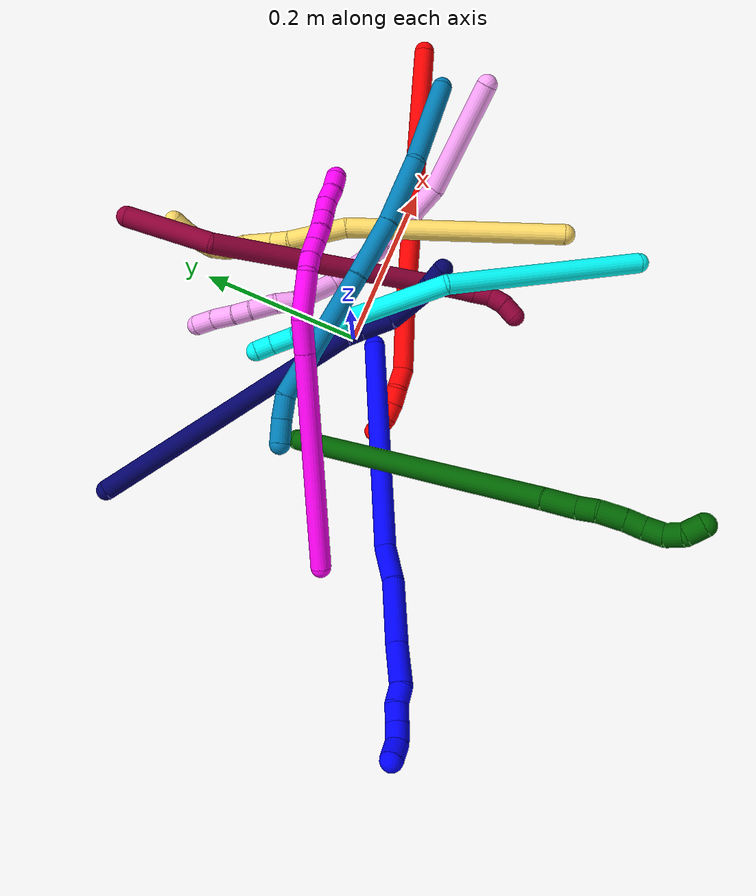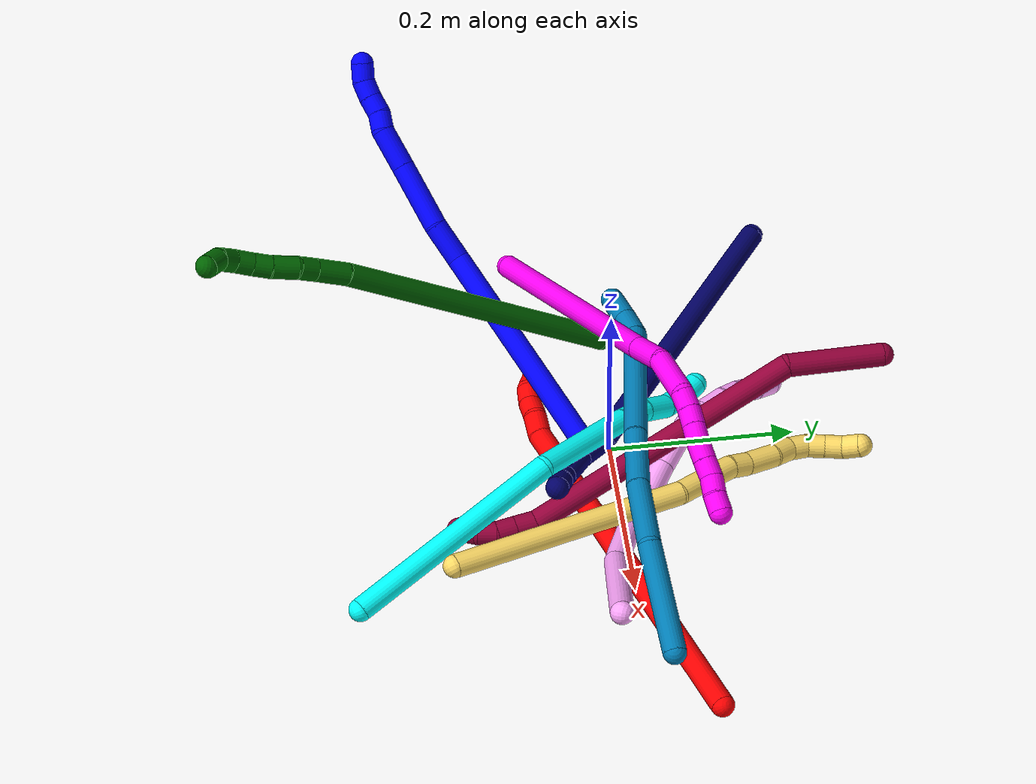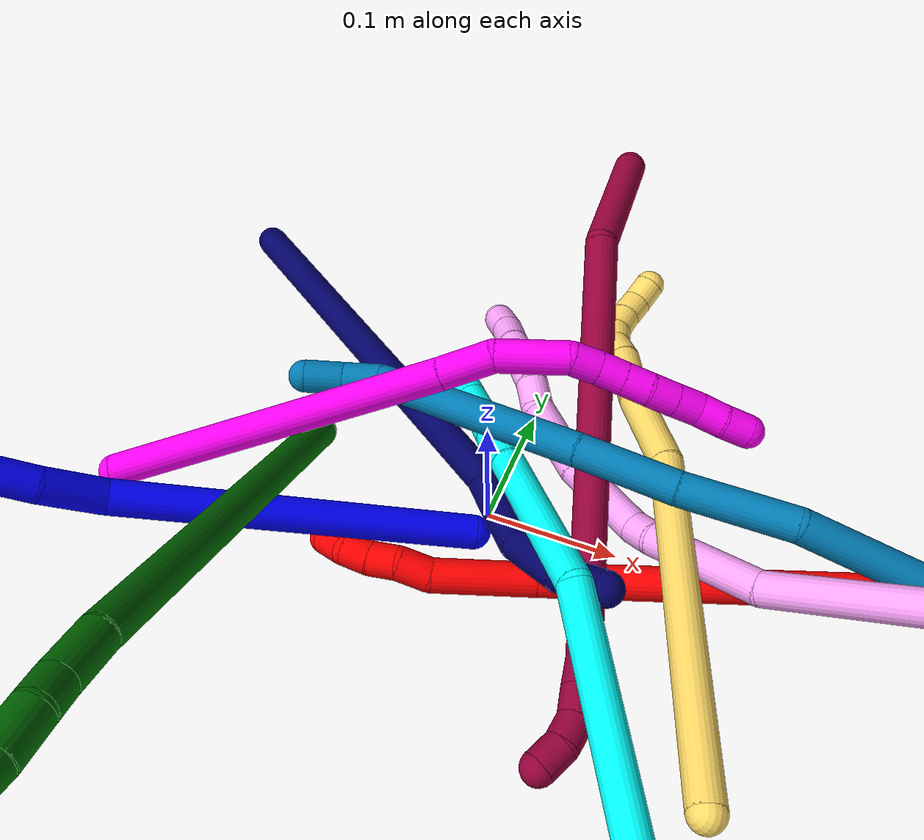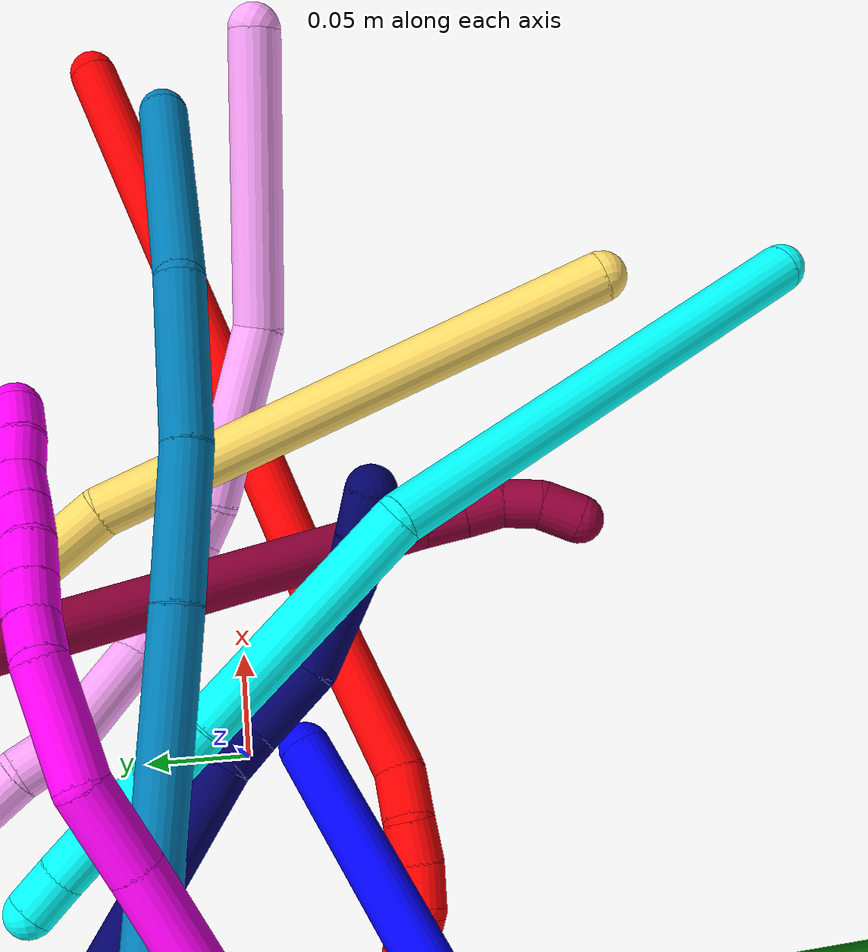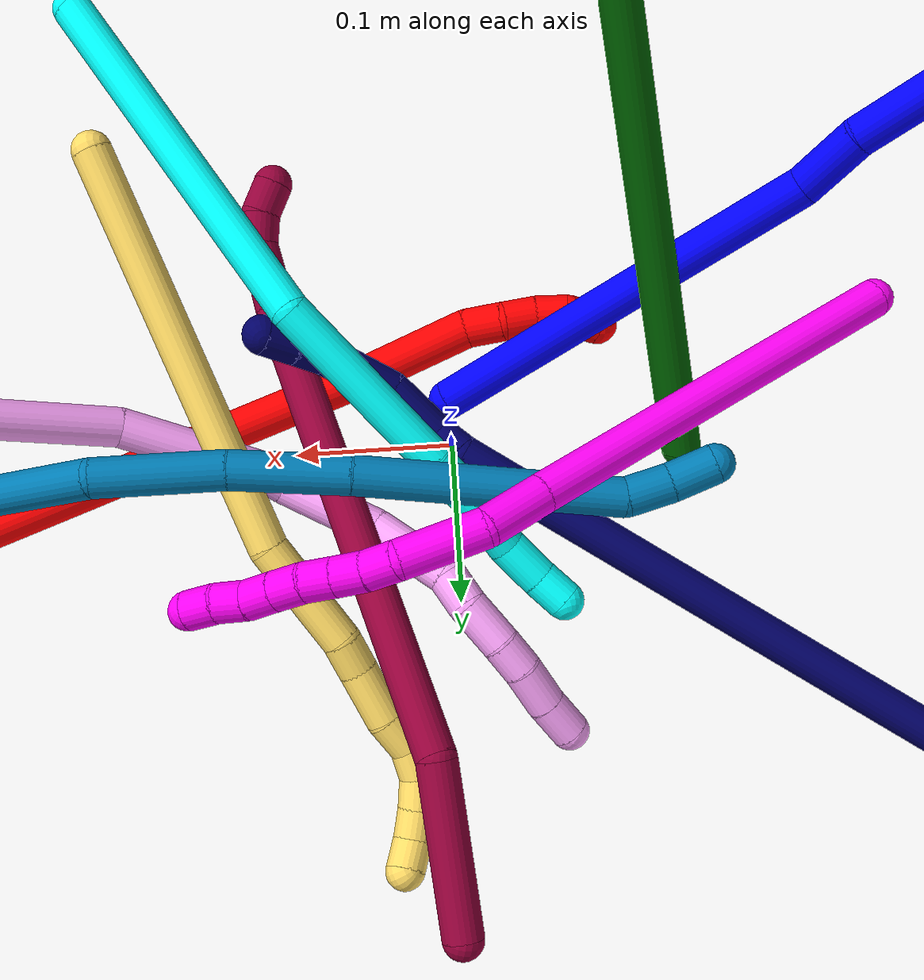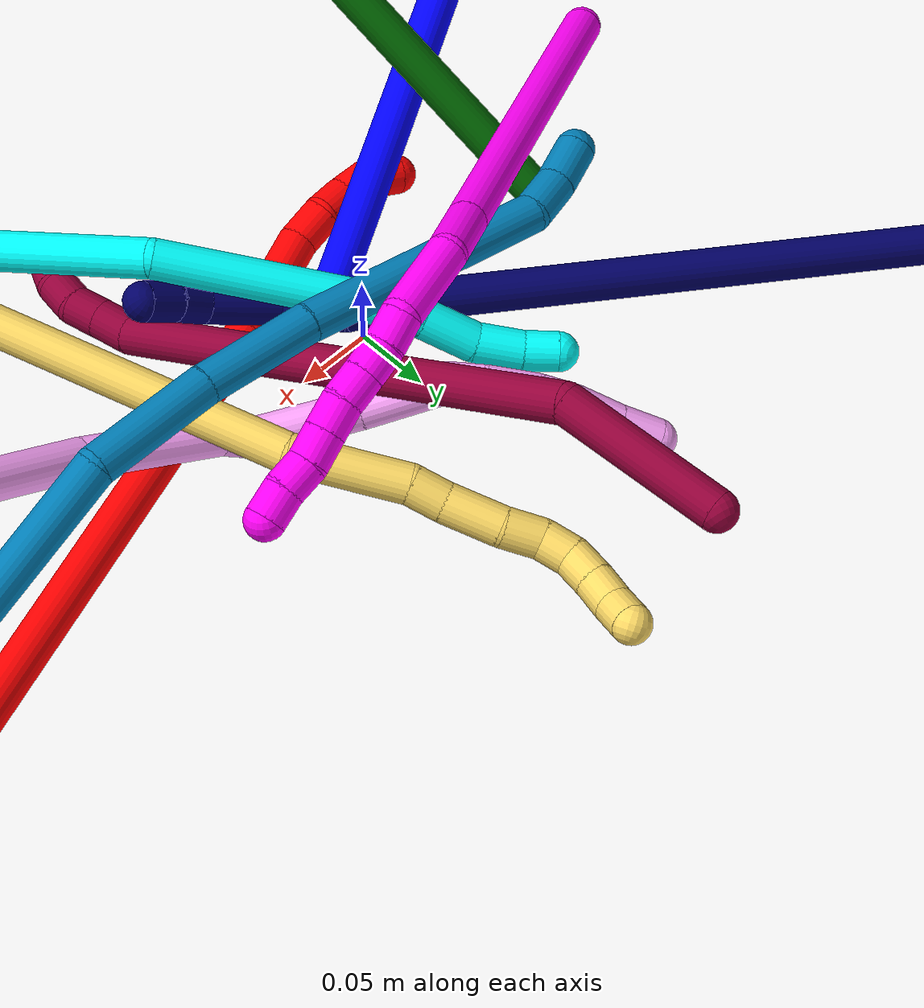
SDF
<sdf version="1.7">
 <world name="default">
  <plugin name="TubeGeneratorPlugin" filename="libtube_generator_plugin.so"/>
  <model name="photoneo_s_sensor">
   <static>1</static>
   <pose>0 0 2 1.57079 1.57079 3.14159</pose>
   <link name="link">
    <inertial><mass>0.1</mass></inertial>
    <sensor name="sensor" type="depth">
     <update_rate>30</update_rate>
     <camera>
      <horizontal_fov>1.22</horizontal_fov>
      <image><width>1920</width><height>1200</height><format>B8G8R8</format></image>
      <clip><near>0.1</near><far>2</far></clip>
      <depth_camera><output>points</output></depth_camera>
     </camera>
     <plugin name="camera_plugin" filename="libgazebo_ros_depth_camera.so">
      <baseline>0.2</baseline>
      <alwaysOn>1</alwaysOn>
      <updateRate>0.0</updateRate>
      <cameraName>camera_ir</cameraName>
      <imageTopicName>/camera/color/image_raw</imageTopicName>
      <cameraInfoTopicName>/camera/color/camera_info</cameraInfoTopicName>
      <depthImageTopicName>/camera/depth/image_raw</depthImageTopicName>
      <depthImageCameraInfoTopicName>/camera/depth/camera_info</depthImageCameraInfoTopicName>
      <pointCloudTopicName>/camera/depth/points</pointCloudTopicName>
      <frameName>fr_optical</frameName>
      <pointCloudCutoff>0.1</pointCloudCutoff>
      <pointCloudCutoffMax>2.0</pointCloudCutoffMax>
      <distortionK1>0</distortionK1>
      <distortionK2>0</distortionK2>
      <distortionK3>0</distortionK3>
      <distortionT1>0</distortionT1>
      <distortionT2>0</distortionT2>
      <CxPrime>0</CxPrime>
      <Cx>0</Cx>
      <Cy>0</Cy>
      <focalLength>0</focalLength>
      <hackBaseline>0</hackBaseline>
     </plugin>
    </sensor>
   </link>
  </model>
  <gravity>0 0 -9.8</gravity>
  <magnetic_field>6e-06 2.3e-05 -4.2e-05</magnetic_field>
  <atmosphere type="adiabatic"/>
  <physics name="default_physics" default="0" type="ode">
   <max_step_size>0.003</max_step_size>
   <real_time_factor>1</real_time_factor>
   <real_time_update_rate>1000</real_time_update_rate>
   <max_contacts>10000</max_contacts>
   <ode>
    <solver>
     <type>quick</type>
     <iters>100</iters>
     <sor>1.3</sor>
     <use_dynamic_moi_rescaling>0</use_dynamic_moi_rescaling>
    </solver>
    <constraints>
     <contact_max_correcting_vel>0</contact_max_correcting_vel>
     <contact_surface_layer>0.001</contact_surface_layer>
     <cfm>0</cfm>
     <erp>0.2</erp>
    </constraints>
   </ode>
  </physics>
  <scene><ambient>0.4 0.4 0.4 1</ambient><background>0.7 0.7 0.7 1</background><shadows>0</shadows></scene>
  <audio><device>default</device></audio>
  <spherical_coordinates>
   <surface_model>EARTH_WGS84</surface_model>
   <latitude_deg>0</latitude_deg>
   <longitude_deg>0</longitude_deg>
   <elevation>0</elevation>
   <heading_deg>0</heading_deg>
  </spherical_coordinates>
  <model name="bin">
   <static>1</static>
   <link name="bottom">
    <collision name="collision-bottom">
     <pose>0 0 -0.01 0 -0 0</pose>
     <geometry><box><size>0.8 0.6 0.02</size></box></geometry>
     <surface>
      <friction><ode><mu>100</mu><mu2>100</mu2></ode></friction>
      <contact><collide_bitmask>65535</collide_bitmask></contact>
     </surface>
    </collision>
   </link>
   <link name="west_wall">
    <collision name="collision-west_wall">
     <pose>-0.41 0 0.1 0 -0 0</pose>
     <geometry><box><size>0.02 0.6 0.2</size></box></geometry>
     <surface>
      <friction><ode><mu>100</mu><mu2>100</mu2></ode></friction>
      <contact><collide_bitmask>65535</collide_bitmask></contact>
     </surface>
    </collision>
   </link>
   <link name="east_wall">
    <collision name="collision-east_wall">
     <pose>0.41 0 0.1 0 -0 0</pose>
     <geometry><box><size>0.02 0.6 0.2</size></box></geometry>
     <surface>
      <friction><ode><mu>100</mu><mu2>100</mu2></ode></friction>
      <contact><collide_bitmask>65535</collide_bitmask></contact>
     </surface>
    </collision>
   </link>
   <link name="south_wall">
    <collision name="collision-south_wall">
     <pose>0 -0.31 0.1 0 -0 0</pose>
     <geometry><box><size>0.8 0.02 0.2</size></box></geometry>
     <surface>
      <friction><ode><mu>100</mu><mu2>100</mu2></ode></friction>
      <contact><collide_bitmask>65535</collide_bitmask></contact>
     </surface>
    </collision>
   </link>
   <link name="north_wall">
    <collision name="collision-north_wall">
     <pose>0 0.31 0.1 0 -0 0</pose>
     <geometry><box><size>0.8 0.02 0.2</size></box></geometry>
     <surface>
      <friction><ode><mu>100</mu><mu2>100</mu2></ode></friction>
      <contact><collide_bitmask>65535</collide_bitmask></contact>
     </surface>
    </collision>
   </link>
  </model>
  <model name="1">
   <static>0</static>
   <link name="1">
    <collision name="collision-cylinder-e_1_1_4">
     <pose>-0.043396 -0.037491 0.113755 0.318365 -0.347603 -0.056358</pose>
     <geometry><cylinder><radius>0.0125</radius><length>0.254785</length></cylinder></geometry>
     <surface>
      <friction><ode><mu>1.16</mu><mu2>1.16</mu2><slip1>0</slip1><slip2>0</slip2></ode></friction>
      <contact><ode><kp>1e+06</kp><kd>1</kd><max_vel>0</max_vel><min_depth>0.001</min_depth></ode></contact>
     </surface>
    </collision>
    <visual name="visual-cylinder-e_1_1_4">
     <pose>-0.043396 -0.037491 0.113755 0.318365 -0.347603 -0.056358</pose>
     <geometry><cylinder><radius>0.0125</radius><length>0.254785</length></cylinder></geometry>
     <material><ambient>0 0 1 1</ambient></material>
    </visual>
    <collision name="collision-cylinder-e_2_4_5">
     <pose>-0.098394 -0.08703 0.242344 0.682124 -0.545625 -0.197963</pose>
     <geometry><cylinder><radius>0.0125</radius><length>0.044715</length></cylinder></geometry>
     <surface>
      <friction><ode><mu>1.16</mu><mu2>1.16</mu2><slip1>0</slip1><slip2>0</slip2></ode></friction>
      <contact><ode><kp>1e+06</kp><kd>1</kd><max_vel>0</max_vel><min_depth>0.001</min_depth></ode></contact>
     </surface>
    </collision>
    <visual name="visual-cylinder-e_2_4_5">
     <pose>-0.098394 -0.08703 0.242344 0.682124 -0.545625 -0.197963</pose>
     <geometry><cylinder><radius>0.0125</radius><length>0.044715</length></cylinder></geometry>
     <material><ambient>0 0 1 1</ambient></material>
    </visual>
    <collision name="collision-cylinder-e_3_5_6">
     <pose>-0.123895 -0.117638 0.286466 0.564817 -0.381238 -0.111864</pose>
     <geometry><cylinder><radius>0.0125</radius><length>0.074709</length></cylinder></geometry>
     <surface>
      <friction><ode><mu>1.16</mu><mu2>1.16</mu2><slip1>0</slip1><slip2>0</slip2></ode></friction>
      <contact><ode><kp>1e+06</kp><kd>1</kd><max_vel>0</max_vel><min_depth>0.001</min_depth></ode></contact>
     </surface>
    </collision>
    <visual name="visual-cylinder-e_3_5_6">
     <pose>-0.123895 -0.117638 0.286466 0.564817 -0.381238 -0.111864</pose>
     <geometry><cylinder><radius>0.0125</radius><length>0.074709</length></cylinder></geometry>
     <material><ambient>0 0 1 1</ambient></material>
    </visual>
    <collision name="collision-cylinder-e_4_6_7">
     <pose>-0.147312 -0.148672 0.332248 0.647571 -0.431364 -0.146787</pose>
     <geometry><cylinder><radius>0.0125</radius><length>0.045533</length></cylinder></geometry>
     <surface>
      <friction><ode><mu>1.16</mu><mu2>1.16</mu2><slip1>0</slip1><slip2>0</slip2></ode></friction>
      <contact><ode><kp>1e+06</kp><kd>1</kd><max_vel>0</max_vel><min_depth>0.001</min_depth></ode></contact>
     </surface>
    </collision>
    <visual name="visual-cylinder-e_4_6_7">
     <pose>-0.147312 -0.148672 0.332248 0.647571 -0.431364 -0.146787</pose>
     <geometry><cylinder><radius>0.0125</radius><length>0.045533</length></cylinder></geometry>
     <material><ambient>0 0 1 1</ambient></material>
    </visual>
    <collision name="collision-cylinder-e_5_7_8">
     <pose>-0.157673 -0.166977 0.35689 0.621025 -0.083897 -0.026936</pose>
     <geometry><cylinder><radius>0.0125</radius><length>0.020108</length></cylinder></geometry>
     <surface>
      <friction><ode><mu>1.16</mu><mu2>1.16</mu2><slip1>0</slip1><slip2>0</slip2></ode></friction>
      <contact><ode><kp>1e+06</kp><kd>1</kd><max_vel>0</max_vel><min_depth>0.001</min_depth></ode></contact>
     </surface>
    </collision>
    <visual name="visual-cylinder-e_5_7_8">
     <pose>-0.157673 -0.166977 0.35689 0.621025 -0.083897 -0.026936</pose>
     <geometry><cylinder><radius>0.0125</radius><length>0.020108</length></cylinder></geometry>
     <material><ambient>0 0 1 1</ambient></material>
    </visual>
    <collision name="collision-cylinder-e_6_8_9">
     <pose>-0.16207 -0.177378 0.373217 0.509609 -0.362563 -0.095411</pose>
     <geometry><cylinder><radius>0.0125</radius><length>0.020044</length></cylinder></geometry>
     <surface>
      <friction><ode><mu>1.16</mu><mu2>1.16</mu2><slip1>0</slip1><slip2>0</slip2></ode></friction>
      <contact><ode><kp>1e+06</kp><kd>1</kd><max_vel>0</max_vel><min_depth>0.001</min_depth></ode></contact>
     </surface>
    </collision>
    <visual name="visual-cylinder-e_6_8_9">
     <pose>-0.16207 -0.177378 0.373217 0.509609 -0.362563 -0.095411</pose>
     <geometry><cylinder><radius>0.0125</radius><length>0.020044</length></cylinder></geometry>
     <material><ambient>0 0 1 1</ambient></material>
    </visual>
    <collision name="collision-cylinder-e_7_9_10">
     <pose>-0.168773 -0.187836 0.388905 0.664906 -0.318772 -0.110889</pose>
     <geometry><cylinder><radius>0.0125</radius><length>0.020093</length></cylinder></geometry>
     <surface>
      <friction><ode><mu>1.16</mu><mu2>1.16</mu2><slip1>0</slip1><slip2>0</slip2></ode></friction>
      <contact><ode><kp>1e+06</kp><kd>1</kd><max_vel>0</max_vel><min_depth>0.001</min_depth></ode></contact>
     </surface>
    </collision>
    <visual name="visual-cylinder-e_7_9_10">
     <pose>-0.168773 -0.187836 0.388905 0.664906 -0.318772 -0.110889</pose>
     <geometry><cylinder><radius>0.0125</radius><length>0.020093</length></cylinder></geometry>
     <material><ambient>0 0 1 1</ambient></material>
    </visual>
    <collision name="collision-cylinder-e_8_10_2">
     <pose>-0.17269 -0.201858 0.402188 0.953504 -0.076852 -0.039708</pose>
     <geometry><cylinder><radius>0.0125</radius><length>0.020014</length></cylinder></geometry>
     <surface>
      <friction><ode><mu>1.16</mu><mu2>1.16</mu2><slip1>0</slip1><slip2>0</slip2></ode></friction>
      <contact><ode><kp>1e+06</kp><kd>1</kd><max_vel>0</max_vel><min_depth>0.001</min_depth></ode></contact>
     </surface>
    </collision>
    <visual name="visual-cylinder-e_8_10_2">
     <pose>-0.17269 -0.201858 0.402188 0.953504 -0.076852 -0.039708</pose>
     <geometry><cylinder><radius>0.0125</radius><length>0.020014</length></cylinder></geometry>
     <material><ambient>0 0 1 1</ambient></material>
    </visual>
    <collision name="collision-sphere-2">
     <pose>-0.173458 -0.209994 0.407964 0 -0 0</pose>
     <geometry><sphere><radius>0.0125</radius></sphere></geometry>
     <surface>
      <friction><ode><mu>1.16</mu><mu2>1.16</mu2><slip1>0</slip1><slip2>0</slip2></ode></friction>
      <contact><ode><kp>1e+06</kp><kd>1</kd><max_vel>0</max_vel><min_depth>0.001</min_depth></ode></contact>
     </surface>
    </collision>
    <visual name="visual-sphere-2">
     <pose>-0.173458 -0.209994 0.407964 0 -0 0</pose>
     <geometry><sphere><radius>0.0125</radius></sphere></geometry>
     <material><ambient>0 0 1 1</ambient></material>
    </visual>
    <collision name="collision-sphere-10">
     <pose>-0.171922 -0.193722 0.396413 0 -0 0</pose>
     <geometry><sphere><radius>0.0125</radius></sphere></geometry>
     <surface>
      <friction><ode><mu>1.16</mu><mu2>1.16</mu2><slip1>0</slip1><slip2>0</slip2></ode></friction>
      <contact><ode><kp>1e+06</kp><kd>1</kd><max_vel>0</max_vel><min_depth>0.001</min_depth></ode></contact>
     </surface>
    </collision>
    <visual name="visual-sphere-10">
     <pose>-0.171922 -0.193722 0.396413 0 -0 0</pose>
     <geometry><sphere><radius>0.0125</radius></sphere></geometry>
     <material><ambient>0 0 1 1</ambient></material>
    </visual>
    <collision name="collision-sphere-9">
     <pose>-0.165625 -0.181949 0.381397 0 -0 0</pose>
     <geometry><sphere><radius>0.0125</radius></sphere></geometry>
     <surface>
      <friction><ode><mu>1.16</mu><mu2>1.16</mu2><slip1>0</slip1><slip2>0</slip2></ode></friction>
      <contact><ode><kp>1e+06</kp><kd>1</kd><max_vel>0</max_vel><min_depth>0.001</min_depth></ode></contact>
     </surface>
    </collision>
    <visual name="visual-sphere-9">
     <pose>-0.165625 -0.181949 0.381397 0 -0 0</pose>
     <geometry><sphere><radius>0.0125</radius></sphere></geometry>
     <material><ambient>0 0 1 1</ambient></material>
    </visual>
    <collision name="collision-sphere-4">
     <pose>-0.086791 -0.074982 0.227509 0 -0 0</pose>
     <geometry><sphere><radius>0.0125</radius></sphere></geometry>
     <surface>
      <friction><ode><mu>1.16</mu><mu2>1.16</mu2><slip1>0</slip1><slip2>0</slip2></ode></friction>
      <contact><ode><kp>1e+06</kp><kd>1</kd><max_vel>0</max_vel><min_depth>0.001</min_depth></ode></contact>
     </surface>
    </collision>
    <visual name="visual-sphere-4">
     <pose>-0.086791 -0.074982 0.227509 0 -0 0</pose>
     <geometry><sphere><radius>0.0125</radius></sphere></geometry>
     <material><ambient>0 0 1 1</ambient></material>
    </visual>
    <collision name="collision-sphere-1">
     <geometry><sphere><radius>0.0125</radius></sphere></geometry>
     <surface>
      <friction><ode><mu>1.16</mu><mu2>1.16</mu2><slip1>0</slip1><slip2>0</slip2></ode></friction>
      <contact><ode><kp>1e+06</kp><kd>1</kd><max_vel>0</max_vel><min_depth>0.001</min_depth></ode></contact>
     </surface>
    </collision>
    <visual name="visual-sphere-1">
     <geometry><sphere><radius>0.0125</radius></sphere></geometry>
     <material><ambient>0 0 1 1</ambient></material>
    </visual>
    <collision name="collision-sphere-8">
     <pose>-0.158516 -0.172807 0.365038 0 -0 0</pose>
     <geometry><sphere><radius>0.0125</radius></sphere></geometry>
     <surface>
      <friction><ode><mu>1.16</mu><mu2>1.16</mu2><slip1>0</slip1><slip2>0</slip2></ode></friction>
      <contact><ode><kp>1e+06</kp><kd>1</kd><max_vel>0</max_vel><min_depth>0.001</min_depth></ode></contact>
     </surface>
    </collision>
    <visual name="visual-sphere-8">
     <pose>-0.158516 -0.172807 0.365038 0 -0 0</pose>
     <geometry><sphere><radius>0.0125</radius></sphere></geometry>
     <material><ambient>0 0 1 1</ambient></material>
    </visual>
    <collision name="collision-sphere-5">
     <pose>-0.109996 -0.099079 0.257179 0 -0 0</pose>
     <geometry><sphere><radius>0.0125</radius></sphere></geometry>
     <surface>
      <friction><ode><mu>1.16</mu><mu2>1.16</mu2><slip1>0</slip1><slip2>0</slip2></ode></friction>
      <contact><ode><kp>1e+06</kp><kd>1</kd><max_vel>0</max_vel><min_depth>0.001</min_depth></ode></contact>
     </surface>
    </collision>
    <visual name="visual-sphere-5">
     <pose>-0.109996 -0.099079 0.257179 0 -0 0</pose>
     <geometry><sphere><radius>0.0125</radius></sphere></geometry>
     <material><ambient>0 0 1 1</ambient></material>
    </visual>
    <collision name="collision-sphere-6">
     <pose>-0.137793 -0.136196 0.315754 0 -0 0</pose>
     <geometry><sphere><radius>0.0125</radius></sphere></geometry>
     <surface>
      <friction><ode><mu>1.16</mu><mu2>1.16</mu2><slip1>0</slip1><slip2>0</slip2></ode></friction>
      <contact><ode><kp>1e+06</kp><kd>1</kd><max_vel>0</max_vel><min_depth>0.001</min_depth></ode></contact>
     </surface>
    </collision>
    <visual name="visual-sphere-6">
     <pose>-0.137793 -0.136196 0.315754 0 -0 0</pose>
     <geometry><sphere><radius>0.0125</radius></sphere></geometry>
     <material><ambient>0 0 1 1</ambient></material>
    </visual>
    <collision name="collision-sphere-7">
     <pose>-0.156831 -0.161148 0.348742 0 -0 0</pose>
     <geometry><sphere><radius>0.0125</radius></sphere></geometry>
     <surface>
      <friction><ode><mu>1.16</mu><mu2>1.16</mu2><slip1>0</slip1><slip2>0</slip2></ode></friction>
      <contact><ode><kp>1e+06</kp><kd>1</kd><max_vel>0</max_vel><min_depth>0.001</min_depth></ode></contact>
     </surface>
    </collision>
    <visual name="visual-sphere-7">
     <pose>-0.156831 -0.161148 0.348742 0 -0 0</pose>
     <geometry><sphere><radius>0.0125</radius></sphere></geometry>
     <material><ambient>0 0 1 1</ambient></material>
    </visual>
    <inertial>
     <pose>-0.089372 -0.087457 0.213739 0 -0 0</pose>
     <mass>0.5</mass>
     <inertia><ixx>0.001266</ixx><ixy>0</ixy><ixz>0</ixz><iyy>0.00128</iyy><iyz>0</iyz><izz>0.00097</izz></inertia>
    </inertial>
   </link>
   <pose>0.000179 -0.028524 0.017077 -1.68336 0.275795 1.73625</pose>
  </model>
  <model name="2">
   <static>0</static>
   <link name="2">
    <collision name="collision-cylinder-e_1_1_4">
     <pose>-0.118932 -0.030926 -0.116612 2.88236 -0.778257 -2.52601</pose>
     <geometry><cylinder><radius>0.0125</radius><length>0.338819</length></cylinder></geometry>
     <surface>
      <friction><ode><mu>1.16</mu><mu2>1.16</mu2><slip1>0</slip1><slip2>0</slip2></ode></friction>
      <contact><ode><kp>1e+06</kp><kd>1</kd><max_vel>0</max_vel><min_depth>0.001</min_depth></ode></contact>
     </surface>
    </collision>
    <visual name="visual-cylinder-e_1_1_4">
     <pose>-0.118932 -0.030926 -0.116612 2.88236 -0.778257 -2.52601</pose>
     <geometry><cylinder><radius>0.0125</radius><length>0.338819</length></cylinder></geometry>
     <material><ambient>1 0 0 1</ambient></material>
    </visual>
    <collision name="collision-cylinder-e_2_4_5">
     <pose>-0.265172 -0.071281 -0.257255 2.76765 -0.813494 -2.31397</pose>
     <geometry><cylinder><radius>0.0125</radius><length>0.075159</length></cylinder></geometry>
     <surface>
      <friction><ode><mu>1.16</mu><mu2>1.16</mu2><slip1>0</slip1><slip2>0</slip2></ode></friction>
      <contact><ode><kp>1e+06</kp><kd>1</kd><max_vel>0</max_vel><min_depth>0.001</min_depth></ode></contact>
     </surface>
    </collision>
    <visual name="visual-cylinder-e_2_4_5">
     <pose>-0.265172 -0.071281 -0.257255 2.76765 -0.813494 -2.31397</pose>
     <geometry><cylinder><radius>0.0125</radius><length>0.075159</length></cylinder></geometry>
     <material><ambient>1 0 0 1</ambient></material>
    </visual>
    <collision name="collision-cylinder-e_3_5_6">
     <pose>-0.303355 -0.081715 -0.286596 2.9548 -1.10964 -2.84158</pose>
     <geometry><cylinder><radius>0.0125</radius><length>0.024284</length></cylinder></geometry>
     <surface>
      <friction><ode><mu>1.16</mu><mu2>1.16</mu2><slip1>0</slip1><slip2>0</slip2></ode></friction>
      <contact><ode><kp>1e+06</kp><kd>1</kd><max_vel>0</max_vel><min_depth>0.001</min_depth></ode></contact>
     </surface>
    </collision>
    <visual name="visual-cylinder-e_3_5_6">
     <pose>-0.303355 -0.081715 -0.286596 2.9548 -1.10964 -2.84158</pose>
     <geometry><cylinder><radius>0.0125</radius><length>0.024284</length></cylinder></geometry>
     <material><ambient>1 0 0 1</ambient></material>
    </visual>
    <collision name="collision-cylinder-e_4_6_7">
     <pose>-0.321776 -0.082399 -0.298985 -3.09657 -0.81689 3.03763</pose>
     <geometry><cylinder><radius>0.0125</radius><length>0.020707</length></cylinder></geometry>
     <surface>
      <friction><ode><mu>1.16</mu><mu2>1.16</mu2><slip1>0</slip1><slip2>0</slip2></ode></friction>
      <contact><ode><kp>1e+06</kp><kd>1</kd><max_vel>0</max_vel><min_depth>0.001</min_depth></ode></contact>
     </surface>
    </collision>
    <visual name="visual-cylinder-e_4_6_7">
     <pose>-0.321776 -0.082399 -0.298985 -3.09657 -0.81689 3.03763</pose>
     <geometry><cylinder><radius>0.0125</radius><length>0.020707</length></cylinder></geometry>
     <material><ambient>1 0 0 1</ambient></material>
    </visual>
    <collision name="collision-cylinder-e_5_7_8">
     <pose>-0.337755 -0.080874 -0.31151 -2.92357 -0.986304 2.73981</pose>
     <geometry><cylinder><radius>0.0125</radius><length>0.020218</length></cylinder></geometry>
     <surface>
      <friction><ode><mu>1.16</mu><mu2>1.16</mu2><slip1>0</slip1><slip2>0</slip2></ode></friction>
      <contact><ode><kp>1e+06</kp><kd>1</kd><max_vel>0</max_vel><min_depth>0.001</min_depth></ode></contact>
     </surface>
    </collision>
    <visual name="visual-cylinder-e_5_7_8">
     <pose>-0.337755 -0.080874 -0.31151 -2.92357 -0.986304 2.73981</pose>
     <geometry><cylinder><radius>0.0125</radius><length>0.020218</length></cylinder></geometry>
     <material><ambient>1 0 0 1</ambient></material>
    </visual>
    <collision name="collision-cylinder-e_6_8_2">
     <pose>-0.352913 -0.074376 -0.322876 -2.41225 -0.702916 1.53055</pose>
     <geometry><cylinder><radius>0.0125</radius><length>0.020814</length></cylinder></geometry>
     <surface>
      <friction><ode><mu>1.16</mu><mu2>1.16</mu2><slip1>0</slip1><slip2>0</slip2></ode></friction>
      <contact><ode><kp>1e+06</kp><kd>1</kd><max_vel>0</max_vel><min_depth>0.001</min_depth></ode></contact>
     </surface>
    </collision>
    <visual name="visual-cylinder-e_6_8_2">
     <pose>-0.352913 -0.074376 -0.322876 -2.41225 -0.702916 1.53055</pose>
     <geometry><cylinder><radius>0.0125</radius><length>0.020814</length></cylinder></geometry>
     <material><ambient>1 0 0 1</ambient></material>
    </visual>
    <collision name="collision-sphere-2">
     <pose>-0.359641 -0.069085 -0.328796 0 -0 0</pose>
     <geometry><sphere><radius>0.0125</radius></sphere></geometry>
     <surface>
      <friction><ode><mu>1.16</mu><mu2>1.16</mu2><slip1>0</slip1><slip2>0</slip2></ode></friction>
      <contact><ode><kp>1e+06</kp><kd>1</kd><max_vel>0</max_vel><min_depth>0.001</min_depth></ode></contact>
     </surface>
    </collision>
    <visual name="visual-sphere-2">
     <pose>-0.359641 -0.069085 -0.328796 0 -0 0</pose>
     <geometry><sphere><radius>0.0125</radius></sphere></geometry>
     <material><ambient>1 0 0 1</ambient></material>
    </visual>
    <collision name="collision-sphere-4">
     <pose>-0.237864 -0.061851 -0.233224 0 -0 0</pose>
     <geometry><sphere><radius>0.0125</radius></sphere></geometry>
     <surface>
      <friction><ode><mu>1.16</mu><mu2>1.16</mu2><slip1>0</slip1><slip2>0</slip2></ode></friction>
      <contact><ode><kp>1e+06</kp><kd>1</kd><max_vel>0</max_vel><min_depth>0.001</min_depth></ode></contact>
     </surface>
    </collision>
    <visual name="visual-sphere-4">
     <pose>-0.237864 -0.061851 -0.233224 0 -0 0</pose>
     <geometry><sphere><radius>0.0125</radius></sphere></geometry>
     <material><ambient>1 0 0 1</ambient></material>
    </visual>
    <collision name="collision-sphere-1">
     <geometry><sphere><radius>0.0125</radius></sphere></geometry>
     <surface>
      <friction><ode><mu>1.16</mu><mu2>1.16</mu2><slip1>0</slip1><slip2>0</slip2></ode></friction>
      <contact><ode><kp>1e+06</kp><kd>1</kd><max_vel>0</max_vel><min_depth>0.001</min_depth></ode></contact>
     </surface>
    </collision>
    <visual name="visual-sphere-1">
     <geometry><sphere><radius>0.0125</radius></sphere></geometry>
     <material><ambient>1 0 0 1</ambient></material>
    </visual>
    <collision name="collision-sphere-8">
     <pose>-0.346186 -0.079667 -0.316956 0 -0 0</pose>
     <geometry><sphere><radius>0.0125</radius></sphere></geometry>
     <surface>
      <friction><ode><mu>1.16</mu><mu2>1.16</mu2><slip1>0</slip1><slip2>0</slip2></ode></friction>
      <contact><ode><kp>1e+06</kp><kd>1</kd><max_vel>0</max_vel><min_depth>0.001</min_depth></ode></contact>
     </surface>
    </collision>
    <visual name="visual-sphere-8">
     <pose>-0.346186 -0.079667 -0.316956 0 -0 0</pose>
     <geometry><sphere><radius>0.0125</radius></sphere></geometry>
     <material><ambient>1 0 0 1</ambient></material>
    </visual>
    <collision name="collision-sphere-5">
     <pose>-0.292481 -0.080711 -0.281287 0 -0 0</pose>
     <geometry><sphere><radius>0.0125</radius></sphere></geometry>
     <surface>
      <friction><ode><mu>1.16</mu><mu2>1.16</mu2><slip1>0</slip1><slip2>0</slip2></ode></friction>
      <contact><ode><kp>1e+06</kp><kd>1</kd><max_vel>0</max_vel><min_depth>0.001</min_depth></ode></contact>
     </surface>
    </collision>
    <visual name="visual-sphere-5">
     <pose>-0.292481 -0.080711 -0.281287 0 -0 0</pose>
     <geometry><sphere><radius>0.0125</radius></sphere></geometry>
     <material><ambient>1 0 0 1</ambient></material>
    </visual>
    <collision name="collision-sphere-6">
     <pose>-0.314228 -0.082718 -0.291905 0 -0 0</pose>
     <geometry><sphere><radius>0.0125</radius></sphere></geometry>
     <surface>
      <friction><ode><mu>1.16</mu><mu2>1.16</mu2><slip1>0</slip1><slip2>0</slip2></ode></friction>
      <contact><ode><kp>1e+06</kp><kd>1</kd><max_vel>0</max_vel><min_depth>0.001</min_depth></ode></contact>
     </surface>
    </collision>
    <visual name="visual-sphere-6">
     <pose>-0.314228 -0.082718 -0.291905 0 -0 0</pose>
     <geometry><sphere><radius>0.0125</radius></sphere></geometry>
     <material><ambient>1 0 0 1</ambient></material>
    </visual>
    <collision name="collision-sphere-7">
     <pose>-0.329324 -0.08208 -0.306064 0 -0 0</pose>
     <geometry><sphere><radius>0.0125</radius></sphere></geometry>
     <surface>
      <friction><ode><mu>1.16</mu><mu2>1.16</mu2><slip1>0</slip1><slip2>0</slip2></ode></friction>
      <contact><ode><kp>1e+06</kp><kd>1</kd><max_vel>0</max_vel><min_depth>0.001</min_depth></ode></contact>
     </surface>
    </collision>
    <visual name="visual-sphere-7">
     <pose>-0.329324 -0.08208 -0.306064 0 -0 0</pose>
     <geometry><sphere><radius>0.0125</radius></sphere></geometry>
     <material><ambient>1 0 0 1</ambient></material>
    </visual>
    <inertial>
     <pose>-0.17686 -0.045419 -0.170029 0 -0 0</pose>
     <mass>0.5</mass>
     <inertia>
      <ixx>-0.003297</ixx>
      <ixy>0</ixy>
      <ixz>0</ixz>
      <iyy>0.001582</iyy>
      <iyz>0</iyz>
      <izz>0.002895</izz>
     </inertia>
    </inertial>
   </link>
   <pose>0.376282 0.063618 0.015888 -0.56895 0.585964 -0.222635</pose>
  </model>
  <model name="3">
   <static>0</static>
   <link name="3">
    <collision name="collision-cylinder-e_1_1_4">
     <pose>0.019976 0.029253 -0.118805 -2.90016 0.161837 -1.17859</pose>
     <geometry><cylinder><radius>0.0125</radius><length>0.247947</length></cylinder></geometry>
     <surface>
      <friction><ode><mu>1.16</mu><mu2>1.16</mu2><slip1>0</slip1><slip2>0</slip2></ode></friction>
      <contact><ode><kp>1e+06</kp><kd>1</kd><max_vel>0</max_vel><min_depth>0.001</min_depth></ode></contact>
     </surface>
    </collision>
    <visual name="visual-cylinder-e_1_1_4">
     <pose>0.019976 0.029253 -0.118805 -2.90016 0.161837 -1.17859</pose>
     <geometry><cylinder><radius>0.0125</radius><length>0.247947</length></cylinder></geometry>
     <material><ambient>0.003922 1 0.996078 1</ambient></material>
    </visual>
    <collision name="collision-cylinder-e_2_4_5">
     <pose>0.040926 0.097662 -0.287652 -2.47765 0.015332 -0.04447</pose>
     <geometry><cylinder><radius>0.0125</radius><length>0.127094</length></cylinder></geometry>
     <surface>
      <friction><ode><mu>1.16</mu><mu2>1.16</mu2><slip1>0</slip1><slip2>0</slip2></ode></friction>
      <contact><ode><kp>1e+06</kp><kd>1</kd><max_vel>0</max_vel><min_depth>0.001</min_depth></ode></contact>
     </surface>
    </collision>
    <visual name="visual-cylinder-e_2_4_5">
     <pose>0.040926 0.097662 -0.287652 -2.47765 0.015332 -0.04447</pose>
     <geometry><cylinder><radius>0.0125</radius><length>0.127094</length></cylinder></geometry>
     <material><ambient>0.003922 1 0.996078 1</ambient></material>
    </visual>
    <collision name="collision-cylinder-e_3_5_6">
     <pose>0.040541 0.149477 -0.351471 -2.39841 -0.07254 0.185694</pose>
     <geometry><cylinder><radius>0.0125</radius><length>0.037521</length></cylinder></geometry>
     <surface>
      <friction><ode><mu>1.16</mu><mu2>1.16</mu2><slip1>0</slip1><slip2>0</slip2></ode></friction>
      <contact><ode><kp>1e+06</kp><kd>1</kd><max_vel>0</max_vel><min_depth>0.001</min_depth></ode></contact>
     </surface>
    </collision>
    <visual name="visual-cylinder-e_3_5_6">
     <pose>0.040541 0.149477 -0.351471 -2.39841 -0.07254 0.185694</pose>
     <geometry><cylinder><radius>0.0125</radius><length>0.037521</length></cylinder></geometry>
     <material><ambient>0.003922 1 0.996078 1</ambient></material>
    </visual>
    <collision name="collision-cylinder-e_4_6_7">
     <pose>0.035259 0.174524 -0.377493 -2.35041 -0.221527 0.520563</pose>
     <geometry><cylinder><radius>0.0125</radius><length>0.035706</length></cylinder></geometry>
     <surface>
      <friction><ode><mu>1.16</mu><mu2>1.16</mu2><slip1>0</slip1><slip2>0</slip2></ode></friction>
      <contact><ode><kp>1e+06</kp><kd>1</kd><max_vel>0</max_vel><min_depth>0.001</min_depth></ode></contact>
     </surface>
    </collision>
    <visual name="visual-cylinder-e_4_6_7">
     <pose>0.035259 0.174524 -0.377493 -2.35041 -0.221527 0.520563</pose>
     <geometry><cylinder><radius>0.0125</radius><length>0.035706</length></cylinder></geometry>
     <material><ambient>0.003922 1 0.996078 1</ambient></material>
    </visual>
    <collision name="collision-cylinder-e_5_7_8">
     <pose>0.03194 0.196164 -0.401601 -2.47921 0.040126 -0.116575</pose>
     <geometry><cylinder><radius>0.0125</radius><length>0.030117</length></cylinder></geometry>
     <surface>
      <friction><ode><mu>1.16</mu><mu2>1.16</mu2><slip1>0</slip1><slip2>0</slip2></ode></friction>
      <contact><ode><kp>1e+06</kp><kd>1</kd><max_vel>0</max_vel><min_depth>0.001</min_depth></ode></contact>
     </surface>
    </collision>
    <visual name="visual-cylinder-e_5_7_8">
     <pose>0.03194 0.196164 -0.401601 -2.47921 0.040126 -0.116575</pose>
     <geometry><cylinder><radius>0.0125</radius><length>0.030117</length></cylinder></geometry>
     <material><ambient>0.003922 1 0.996078 1</ambient></material>
    </visual>
    <collision name="collision-cylinder-e_6_8_2">
     <pose>0.034508 0.211223 -0.422367 -2.56368 0.182702 -0.597835</pose>
     <geometry><cylinder><radius>0.0125</radius><length>0.021615</length></cylinder></geometry>
     <surface>
      <friction><ode><mu>1.16</mu><mu2>1.16</mu2><slip1>0</slip1><slip2>0</slip2></ode></friction>
      <contact><ode><kp>1e+06</kp><kd>1</kd><max_vel>0</max_vel><min_depth>0.001</min_depth></ode></contact>
     </surface>
    </collision>
    <visual name="visual-cylinder-e_6_8_2">
     <pose>0.034508 0.211223 -0.422367 -2.56368 0.182702 -0.597835</pose>
     <geometry><cylinder><radius>0.0125</radius><length>0.021615</length></cylinder></geometry>
     <material><ambient>0.003922 1 0.996078 1</ambient></material>
    </visual>
    <collision name="collision-sphere-2">
     <pose>0.036471 0.217029 -0.431269 0 -0 0</pose>
     <geometry><sphere><radius>0.0125</radius></sphere></geometry>
     <surface>
      <friction><ode><mu>1.16</mu><mu2>1.16</mu2><slip1>0</slip1><slip2>0</slip2></ode></friction>
      <contact><ode><kp>1e+06</kp><kd>1</kd><max_vel>0</max_vel><min_depth>0.001</min_depth></ode></contact>
     </surface>
    </collision>
    <visual name="visual-sphere-2">
     <pose>0.036471 0.217029 -0.431269 0 -0 0</pose>
     <geometry><sphere><radius>0.0125</radius></sphere></geometry>
     <material><ambient>0.003922 1 0.996078 1</ambient></material>
    </visual>
    <collision name="collision-sphere-4">
     <pose>0.039952 0.058507 -0.23761 0 -0 0</pose>
     <geometry><sphere><radius>0.0125</radius></sphere></geometry>
     <surface>
      <friction><ode><mu>1.16</mu><mu2>1.16</mu2><slip1>0</slip1><slip2>0</slip2></ode></friction>
      <contact><ode><kp>1e+06</kp><kd>1</kd><max_vel>0</max_vel><min_depth>0.001</min_depth></ode></contact>
     </surface>
    </collision>
    <visual name="visual-sphere-4">
     <pose>0.039952 0.058507 -0.23761 0 -0 0</pose>
     <geometry><sphere><radius>0.0125</radius></sphere></geometry>
     <material><ambient>0.003922 1 0.996078 1</ambient></material>
    </visual>
    <collision name="collision-sphere-1">
     <geometry><sphere><radius>0.0125</radius></sphere></geometry>
     <surface>
      <friction><ode><mu>1.16</mu><mu2>1.16</mu2><slip1>0</slip1><slip2>0</slip2></ode></friction>
      <contact><ode><kp>1e+06</kp><kd>1</kd><max_vel>0</max_vel><min_depth>0.001</min_depth></ode></contact>
     </surface>
    </collision>
    <visual name="visual-sphere-1">
     <geometry><sphere><radius>0.0125</radius></sphere></geometry>
     <material><ambient>0.003922 1 0.996078 1</ambient></material>
    </visual>
    <collision name="collision-sphere-8">
     <pose>0.032544 0.205418 -0.413465 0 -0 0</pose>
     <geometry><sphere><radius>0.0125</radius></sphere></geometry>
     <surface>
      <friction><ode><mu>1.16</mu><mu2>1.16</mu2><slip1>0</slip1><slip2>0</slip2></ode></friction>
      <contact><ode><kp>1e+06</kp><kd>1</kd><max_vel>0</max_vel><min_depth>0.001</min_depth></ode></contact>
     </surface>
    </collision>
    <visual name="visual-sphere-8">
     <pose>0.032544 0.205418 -0.413465 0 -0 0</pose>
     <geometry><sphere><radius>0.0125</radius></sphere></geometry>
     <material><ambient>0.003922 1 0.996078 1</ambient></material>
    </visual>
    <collision name="collision-sphere-5">
     <pose>0.041901 0.136817 -0.337694 0 -0 0</pose>
     <geometry><sphere><radius>0.0125</radius></sphere></geometry>
     <surface>
      <friction><ode><mu>1.16</mu><mu2>1.16</mu2><slip1>0</slip1><slip2>0</slip2></ode></friction>
      <contact><ode><kp>1e+06</kp><kd>1</kd><max_vel>0</max_vel><min_depth>0.001</min_depth></ode></contact>
     </surface>
    </collision>
    <visual name="visual-sphere-5">
     <pose>0.041901 0.136817 -0.337694 0 -0 0</pose>
     <geometry><sphere><radius>0.0125</radius></sphere></geometry>
     <material><ambient>0.003922 1 0.996078 1</ambient></material>
    </visual>
    <collision name="collision-sphere-6">
     <pose>0.039181 0.162138 -0.365249 0 -0 0</pose>
     <geometry><sphere><radius>0.0125</radius></sphere></geometry>
     <surface>
      <friction><ode><mu>1.16</mu><mu2>1.16</mu2><slip1>0</slip1><slip2>0</slip2></ode></friction>
      <contact><ode><kp>1e+06</kp><kd>1</kd><max_vel>0</max_vel><min_depth>0.001</min_depth></ode></contact>
     </surface>
    </collision>
    <visual name="visual-sphere-6">
     <pose>0.039181 0.162138 -0.365249 0 -0 0</pose>
     <geometry><sphere><radius>0.0125</radius></sphere></geometry>
     <material><ambient>0.003922 1 0.996078 1</ambient></material>
    </visual>
    <collision name="collision-sphere-7">
     <pose>0.031336 0.18691 -0.389736 0 -0 0</pose>
     <geometry><sphere><radius>0.0125</radius></sphere></geometry>
     <surface>
      <friction><ode><mu>1.16</mu><mu2>1.16</mu2><slip1>0</slip1><slip2>0</slip2></ode></friction>
      <contact><ode><kp>1e+06</kp><kd>1</kd><max_vel>0</max_vel><min_depth>0.001</min_depth></ode></contact>
     </surface>
    </collision>
    <visual name="visual-sphere-7">
     <pose>0.031336 0.18691 -0.389736 0 -0 0</pose>
     <geometry><sphere><radius>0.0125</radius></sphere></geometry>
     <material><ambient>0.003922 1 0.996078 1</ambient></material>
    </visual>
    <inertial>
     <pose>0.029285 0.083958 -0.227814 0 -0 0</pose>
     <mass>0.5</mass>
     <inertia>
      <ixx>-0.000496</ixx>
      <ixy>0</ixy>
      <ixz>0</ixz>
      <iyy>-0.001735</iyy>
      <iyz>0</iyz>
      <izz>-0.000663</izz>
     </inertia>
    </inertial>
   </link>
   <pose>0.220818 -0.288015 0.03518 -1.93528 -0.677376 -2.63319</pose>
  </model>
  <model name="4">
   <static>0</static>
   <link name="4">
    <collision name="collision-cylinder-e_1_1_4">
     <pose>-0.038344 0.050257 -0.028365 -2.08463 -0.58646 0.954497</pose>
     <geometry><cylinder><radius>0.0125</radius><length>0.138572</length></cylinder></geometry>
     <surface>
      <friction><ode><mu>1.16</mu><mu2>1.16</mu2><slip1>0</slip1><slip2>0</slip2></ode></friction>
      <contact><ode><kp>1e+06</kp><kd>1</kd><max_vel>0</max_vel><min_depth>0.001</min_depth></ode></contact>
     </surface>
    </collision>
    <visual name="visual-cylinder-e_1_1_4">
     <pose>-0.038344 0.050257 -0.028365 -2.08463 -0.58646 0.954497</pose>
     <geometry><cylinder><radius>0.0125</radius><length>0.138572</length></cylinder></geometry>
     <material><ambient>1 0.65098 0.996078 1</ambient></material>
    </visual>
    <collision name="collision-cylinder-e_2_4_5">
     <pose>-0.109365 0.129881 -0.06469 -1.83549 -0.821024 1.03451</pose>
     <geometry><cylinder><radius>0.0125</radius><length>0.089299</length></cylinder></geometry>
     <surface>
      <friction><ode><mu>1.16</mu><mu2>1.16</mu2><slip1>0</slip1><slip2>0</slip2></ode></friction>
      <contact><ode><kp>1e+06</kp><kd>1</kd><max_vel>0</max_vel><min_depth>0.001</min_depth></ode></contact>
     </surface>
    </collision>
    <visual name="visual-cylinder-e_2_4_5">
     <pose>-0.109365 0.129881 -0.06469 -1.83549 -0.821024 1.03451</pose>
     <geometry><cylinder><radius>0.0125</radius><length>0.089299</length></cylinder></geometry>
     <material><ambient>1 0.65098 0.996078 1</ambient></material>
    </visual>
    <collision name="collision-cylinder-e_3_5_6">
     <pose>-0.148811 0.167253 -0.07255 -1.55821 -0.702028 0.693936</pose>
     <geometry><cylinder><radius>0.0125</radius><length>0.020967</length></cylinder></geometry>
     <surface>
      <friction><ode><mu>1.16</mu><mu2>1.16</mu2><slip1>0</slip1><slip2>0</slip2></ode></friction>
      <contact><ode><kp>1e+06</kp><kd>1</kd><max_vel>0</max_vel><min_depth>0.001</min_depth></ode></contact>
     </surface>
    </collision>
    <visual name="visual-cylinder-e_3_5_6">
     <pose>-0.148811 0.167253 -0.07255 -1.55821 -0.702028 0.693936</pose>
     <geometry><cylinder><radius>0.0125</radius><length>0.020967</length></cylinder></geometry>
     <material><ambient>1 0.65098 0.996078 1</ambient></material>
    </visual>
    <collision name="collision-cylinder-e_4_6_7">
     <pose>-0.185574 0.187597 -0.071842 -1.52165 -1.18004 1.13502</pose>
     <geometry><cylinder><radius>0.0125</radius><length>0.064876</length></cylinder></geometry>
     <surface>
      <friction><ode><mu>1.16</mu><mu2>1.16</mu2><slip1>0</slip1><slip2>0</slip2></ode></friction>
      <contact><ode><kp>1e+06</kp><kd>1</kd><max_vel>0</max_vel><min_depth>0.001</min_depth></ode></contact>
     </surface>
    </collision>
    <visual name="visual-cylinder-e_4_6_7">
     <pose>-0.185574 0.187597 -0.071842 -1.52165 -1.18004 1.13502</pose>
     <geometry><cylinder><radius>0.0125</radius><length>0.064876</length></cylinder></geometry>
     <material><ambient>1 0.65098 0.996078 1</ambient></material>
    </visual>
    <collision name="collision-cylinder-e_5_7_8">
     <pose>-0.242699 0.204232 -0.066165 -0.702694 -1.33062 0.560119</pose>
     <geometry><cylinder><radius>0.0125</radius><length>0.055867</length></cylinder></geometry>
     <surface>
      <friction><ode><mu>1.16</mu><mu2>1.16</mu2><slip1>0</slip1><slip2>0</slip2></ode></friction>
      <contact><ode><kp>1e+06</kp><kd>1</kd><max_vel>0</max_vel><min_depth>0.001</min_depth></ode></contact>
     </surface>
    </collision>
    <visual name="visual-cylinder-e_5_7_8">
     <pose>-0.242699 0.204232 -0.066165 -0.702694 -1.33062 0.560119</pose>
     <geometry><cylinder><radius>0.0125</radius><length>0.055867</length></cylinder></geometry>
     <material><ambient>1 0.65098 0.996078 1</ambient></material>
    </visual>
    <collision name="collision-cylinder-e_6_8_9">
     <pose>-0.278978 0.211742 -0.055306 -0.507092 -0.944209 0.263096</pose>
     <geometry><cylinder><radius>0.0125</radius><length>0.022586</length></cylinder></geometry>
     <surface>
      <friction><ode><mu>1.16</mu><mu2>1.16</mu2><slip1>0</slip1><slip2>0</slip2></ode></friction>
      <contact><ode><kp>1e+06</kp><kd>1</kd><max_vel>0</max_vel><min_depth>0.001</min_depth></ode></contact>
     </surface>
    </collision>
    <visual name="visual-cylinder-e_6_8_9">
     <pose>-0.278978 0.211742 -0.055306 -0.507092 -0.944209 0.263096</pose>
     <geometry><cylinder><radius>0.0125</radius><length>0.022586</length></cylinder></geometry>
     <material><ambient>1 0.65098 0.996078 1</ambient></material>
    </visual>
    <collision name="collision-cylinder-e_7_9_10">
     <pose>-0.299815 0.223268 -0.043514 -0.945222 -0.850834 0.455255</pose>
     <geometry><cylinder><radius>0.0125</radius><length>0.031095</length></cylinder></geometry>
     <surface>
      <friction><ode><mu>1.16</mu><mu2>1.16</mu2><slip1>0</slip1><slip2>0</slip2></ode></friction>
      <contact><ode><kp>1e+06</kp><kd>1</kd><max_vel>0</max_vel><min_depth>0.001</min_depth></ode></contact>
     </surface>
    </collision>
    <visual name="visual-cylinder-e_7_9_10">
     <pose>-0.299815 0.223268 -0.043514 -0.945222 -0.850834 0.455255</pose>
     <geometry><cylinder><radius>0.0125</radius><length>0.031095</length></cylinder></geometry>
     <material><ambient>1 0.65098 0.996078 1</ambient></material>
    </visual>
    <collision name="collision-cylinder-e_8_10_11">
     <pose>-0.318608 0.238878 -0.033388 -1.05668 -0.702934 0.421705</pose>
     <geometry><cylinder><radius>0.0125</radius><length>0.021979</length></cylinder></geometry>
     <surface>
      <friction><ode><mu>1.16</mu><mu2>1.16</mu2><slip1>0</slip1><slip2>0</slip2></ode></friction>
      <contact><ode><kp>1e+06</kp><kd>1</kd><max_vel>0</max_vel><min_depth>0.001</min_depth></ode></contact>
     </surface>
    </collision>
    <visual name="visual-cylinder-e_8_10_11">
     <pose>-0.318608 0.238878 -0.033388 -1.05668 -0.702934 0.421705</pose>
     <geometry><cylinder><radius>0.0125</radius><length>0.021979</length></cylinder></geometry>
     <material><ambient>1 0.65098 0.996078 1</ambient></material>
    </visual>
    <collision name="collision-cylinder-e_9_11_12">
     <pose>-0.333267 0.256918 -0.023385 -1.0698 -0.55284 0.333061</pose>
     <geometry><cylinder><radius>0.0125</radius><length>0.028772</length></cylinder></geometry>
     <surface>
      <friction><ode><mu>1.16</mu><mu2>1.16</mu2><slip1>0</slip1><slip2>0</slip2></ode></friction>
      <contact><ode><kp>1e+06</kp><kd>1</kd><max_vel>0</max_vel><min_depth>0.001</min_depth></ode></contact>
     </surface>
    </collision>
    <visual name="visual-cylinder-e_9_11_12">
     <pose>-0.333267 0.256918 -0.023385 -1.0698 -0.55284 0.333061</pose>
     <geometry><cylinder><radius>0.0125</radius><length>0.028772</length></cylinder></geometry>
     <material><ambient>1 0.65098 0.996078 1</ambient></material>
    </visual>
    <collision name="collision-cylinder-e_10_12_2">
     <pose>-0.348192 0.277514 -0.013343 -1.17135 -0.603171 0.406964</pose>
     <geometry><cylinder><radius>0.0125</radius><length>0.025986</length></cylinder></geometry>
     <surface>
      <friction><ode><mu>1.16</mu><mu2>1.16</mu2><slip1>0</slip1><slip2>0</slip2></ode></friction>
      <contact><ode><kp>1e+06</kp><kd>1</kd><max_vel>0</max_vel><min_depth>0.001</min_depth></ode></contact>
     </surface>
    </collision>
    <visual name="visual-cylinder-e_10_12_2">
     <pose>-0.348192 0.277514 -0.013343 -1.17135 -0.603171 0.406964</pose>
     <geometry><cylinder><radius>0.0125</radius><length>0.025986</length></cylinder></geometry>
     <material><ambient>1 0.65098 0.996078 1</ambient></material>
    </visual>
    <collision name="collision-sphere-2">
     <pose>-0.355562 0.287371 -0.009181 0 -0 0</pose>
     <geometry><sphere><radius>0.0125</radius></sphere></geometry>
     <surface>
      <friction><ode><mu>1.16</mu><mu2>1.16</mu2><slip1>0</slip1><slip2>0</slip2></ode></friction>
      <contact><ode><kp>1e+06</kp><kd>1</kd><max_vel>0</max_vel><min_depth>0.001</min_depth></ode></contact>
     </surface>
    </collision>
    <visual name="visual-sphere-2">
     <pose>-0.355562 0.287371 -0.009181 0 -0 0</pose>
     <geometry><sphere><radius>0.0125</radius></sphere></geometry>
     <material><ambient>1 0.65098 0.996078 1</ambient></material>
    </visual>
    <collision name="collision-sphere-12">
     <pose>-0.340821 0.267656 -0.017504 0 -0 0</pose>
     <geometry><sphere><radius>0.0125</radius></sphere></geometry>
     <surface>
      <friction><ode><mu>1.16</mu><mu2>1.16</mu2><slip1>0</slip1><slip2>0</slip2></ode></friction>
      <contact><ode><kp>1e+06</kp><kd>1</kd><max_vel>0</max_vel><min_depth>0.001</min_depth></ode></contact>
     </surface>
    </collision>
    <visual name="visual-sphere-12">
     <pose>-0.340821 0.267656 -0.017504 0 -0 0</pose>
     <geometry><sphere><radius>0.0125</radius></sphere></geometry>
     <material><ambient>1 0.65098 0.996078 1</ambient></material>
    </visual>
    <collision name="collision-sphere-11">
     <pose>-0.325713 0.246179 -0.029265 0 -0 0</pose>
     <geometry><sphere><radius>0.0125</radius></sphere></geometry>
     <surface>
      <friction><ode><mu>1.16</mu><mu2>1.16</mu2><slip1>0</slip1><slip2>0</slip2></ode></friction>
      <contact><ode><kp>1e+06</kp><kd>1</kd><max_vel>0</max_vel><min_depth>0.001</min_depth></ode></contact>
     </surface>
    </collision>
    <visual name="visual-sphere-11">
     <pose>-0.325713 0.246179 -0.029265 0 -0 0</pose>
     <geometry><sphere><radius>0.0125</radius></sphere></geometry>
     <material><ambient>1 0.65098 0.996078 1</ambient></material>
    </visual>
    <collision name="collision-sphere-10">
     <pose>-0.311504 0.231578 -0.037511 0 -0 0</pose>
     <geometry><sphere><radius>0.0125</radius></sphere></geometry>
     <surface>
      <friction><ode><mu>1.16</mu><mu2>1.16</mu2><slip1>0</slip1><slip2>0</slip2></ode></friction>
      <contact><ode><kp>1e+06</kp><kd>1</kd><max_vel>0</max_vel><min_depth>0.001</min_depth></ode></contact>
     </surface>
    </collision>
    <visual name="visual-sphere-10">
     <pose>-0.311504 0.231578 -0.037511 0 -0 0</pose>
     <geometry><sphere><radius>0.0125</radius></sphere></geometry>
     <material><ambient>1 0.65098 0.996078 1</ambient></material>
    </visual>
    <collision name="collision-sphere-9">
     <pose>-0.288126 0.214958 -0.049517 0 -0 0</pose>
     <geometry><sphere><radius>0.0125</radius></sphere></geometry>
     <surface>
      <friction><ode><mu>1.16</mu><mu2>1.16</mu2><slip1>0</slip1><slip2>0</slip2></ode></friction>
      <contact><ode><kp>1e+06</kp><kd>1</kd><max_vel>0</max_vel><min_depth>0.001</min_depth></ode></contact>
     </surface>
    </collision>
    <visual name="visual-sphere-9">
     <pose>-0.288126 0.214958 -0.049517 0 -0 0</pose>
     <geometry><sphere><radius>0.0125</radius></sphere></geometry>
     <material><ambient>1 0.65098 0.996078 1</ambient></material>
    </visual>
    <collision name="collision-sphere-4">
     <pose>-0.076688 0.100513 -0.05673 0 -0 0</pose>
     <geometry><sphere><radius>0.0125</radius></sphere></geometry>
     <surface>
      <friction><ode><mu>1.16</mu><mu2>1.16</mu2><slip1>0</slip1><slip2>0</slip2></ode></friction>
      <contact><ode><kp>1e+06</kp><kd>1</kd><max_vel>0</max_vel><min_depth>0.001</min_depth></ode></contact>
     </surface>
    </collision>
    <visual name="visual-sphere-4">
     <pose>-0.076688 0.100513 -0.05673 0 -0 0</pose>
     <geometry><sphere><radius>0.0125</radius></sphere></geometry>
     <material><ambient>1 0.65098 0.996078 1</ambient></material>
    </visual>
    <collision name="collision-sphere-1">
     <geometry><sphere><radius>0.0125</radius></sphere></geometry>
     <surface>
      <friction><ode><mu>1.16</mu><mu2>1.16</mu2><slip1>0</slip1><slip2>0</slip2></ode></friction>
      <contact><ode><kp>1e+06</kp><kd>1</kd><max_vel>0</max_vel><min_depth>0.001</min_depth></ode></contact>
     </surface>
    </collision>
    <visual name="visual-sphere-1">
     <geometry><sphere><radius>0.0125</radius></sphere></geometry>
     <material><ambient>1 0.65098 0.996078 1</ambient></material>
    </visual>
    <collision name="collision-sphere-8">
     <pose>-0.269831 0.208526 -0.061094 0 -0 0</pose>
     <geometry><sphere><radius>0.0125</radius></sphere></geometry>
     <surface>
      <friction><ode><mu>1.16</mu><mu2>1.16</mu2><slip1>0</slip1><slip2>0</slip2></ode></friction>
      <contact><ode><kp>1e+06</kp><kd>1</kd><max_vel>0</max_vel><min_depth>0.001</min_depth></ode></contact>
     </surface>
    </collision>
    <visual name="visual-sphere-8">
     <pose>-0.269831 0.208526 -0.061094 0 -0 0</pose>
     <geometry><sphere><radius>0.0125</radius></sphere></geometry>
     <material><ambient>1 0.65098 0.996078 1</ambient></material>
    </visual>
    <collision name="collision-sphere-5">
     <pose>-0.142041 0.159249 -0.072651 0 -0 0</pose>
     <geometry><sphere><radius>0.0125</radius></sphere></geometry>
     <surface>
      <friction><ode><mu>1.16</mu><mu2>1.16</mu2><slip1>0</slip1><slip2>0</slip2></ode></friction>
      <contact><ode><kp>1e+06</kp><kd>1</kd><max_vel>0</max_vel><min_depth>0.001</min_depth></ode></contact>
     </surface>
    </collision>
    <visual name="visual-sphere-5">
     <pose>-0.142041 0.159249 -0.072651 0 -0 0</pose>
     <geometry><sphere><radius>0.0125</radius></sphere></geometry>
     <material><ambient>1 0.65098 0.996078 1</ambient></material>
    </visual>
    <collision name="collision-sphere-6">
     <pose>-0.155581 0.175257 -0.072449 0 -0 0</pose>
     <geometry><sphere><radius>0.0125</radius></sphere></geometry>
     <surface>
      <friction><ode><mu>1.16</mu><mu2>1.16</mu2><slip1>0</slip1><slip2>0</slip2></ode></friction>
      <contact><ode><kp>1e+06</kp><kd>1</kd><max_vel>0</max_vel><min_depth>0.001</min_depth></ode></contact>
     </surface>
    </collision>
    <visual name="visual-sphere-6">
     <pose>-0.155581 0.175257 -0.072449 0 -0 0</pose>
     <geometry><sphere><radius>0.0125</radius></sphere></geometry>
     <material><ambient>1 0.65098 0.996078 1</ambient></material>
    </visual>
    <collision name="collision-sphere-7">
     <pose>-0.215567 0.199937 -0.071235 0 -0 0</pose>
     <geometry><sphere><radius>0.0125</radius></sphere></geometry>
     <surface>
      <friction><ode><mu>1.16</mu><mu2>1.16</mu2><slip1>0</slip1><slip2>0</slip2></ode></friction>
      <contact><ode><kp>1e+06</kp><kd>1</kd><max_vel>0</max_vel><min_depth>0.001</min_depth></ode></contact>
     </surface>
    </collision>
    <visual name="visual-sphere-7">
     <pose>-0.215567 0.199937 -0.071235 0 -0 0</pose>
     <geometry><sphere><radius>0.0125</radius></sphere></geometry>
     <material><ambient>1 0.65098 0.996078 1</ambient></material>
    </visual>
    <inertial>
     <pose>-0.170123 0.154457 -0.047883 0 -0 0</pose>
     <mass>0.5</mass>
     <inertia><ixx>0.000327</ixx><ixy>0</ixy><ixz>0</ixz><iyy>0.000331</iyy><iyz>0</iyz><izz>-7e-06</izz></inertia>
    </inertial>
   </link>
   <pose>0.325683 -0.033023 0.115474 -1.41851 0.448088 -0.433428</pose>
  </model>
  <model name="5">
   <static>0</static>
   <link name="5">
    <collision name="collision-cylinder-e_1_1_4">
     <pose>-0.077772 0.105986 0.01343 -1.44475 -0.629259 0.558614</pose>
     <geometry><cylinder><radius>0.0125</radius><length>0.264286</length></cylinder></geometry>
     <surface>
      <friction><ode><mu>1.16</mu><mu2>1.16</mu2><slip1>0</slip1><slip2>0</slip2></ode></friction>
      <contact><ode><kp>1e+06</kp><kd>1</kd><max_vel>0</max_vel><min_depth>0.001</min_depth></ode></contact>
     </surface>
    </collision>
    <visual name="visual-cylinder-e_1_1_4">
     <pose>-0.077772 0.105986 0.01343 -1.44475 -0.629259 0.558614</pose>
     <geometry><cylinder><radius>0.0125</radius><length>0.264286</length></cylinder></geometry>
     <material><ambient>1 0.858824 0.4 1</ambient></material>
    </visual>
    <collision name="collision-cylinder-e_2_4_5">
     <pose>-0.170848 0.244867 0.024591 -1.63965 -0.434514 0.464443</pose>
     <geometry><cylinder><radius>0.0125</radius><length>0.072703</length></cylinder></geometry>
     <surface>
      <friction><ode><mu>1.16</mu><mu2>1.16</mu2><slip1>0</slip1><slip2>0</slip2></ode></friction>
      <contact><ode><kp>1e+06</kp><kd>1</kd><max_vel>0</max_vel><min_depth>0.001</min_depth></ode></contact>
     </surface>
    </collision>
    <visual name="visual-cylinder-e_2_4_5">
     <pose>-0.170848 0.244867 0.024591 -1.63965 -0.434514 0.464443</pose>
     <geometry><cylinder><radius>0.0125</radius><length>0.072703</length></cylinder></geometry>
     <material><ambient>1 0.858824 0.4 1</ambient></material>
    </visual>
    <collision name="collision-cylinder-e_3_5_6">
     <pose>-0.190253 0.287991 0.024267 -1.38298 -0.375374 0.311899</pose>
     <geometry><cylinder><radius>0.0125</radius><length>0.022382</length></cylinder></geometry>
     <surface>
      <friction><ode><mu>1.16</mu><mu2>1.16</mu2><slip1>0</slip1><slip2>0</slip2></ode></friction>
      <contact><ode><kp>1e+06</kp><kd>1</kd><max_vel>0</max_vel><min_depth>0.001</min_depth></ode></contact>
     </surface>
    </collision>
    <visual name="visual-cylinder-e_3_5_6">
     <pose>-0.190253 0.287991 0.024267 -1.38298 -0.375374 0.311899</pose>
     <geometry><cylinder><radius>0.0125</radius><length>0.022382</length></cylinder></geometry>
     <material><ambient>1 0.858824 0.4 1</ambient></material>
    </visual>
    <collision name="collision-cylinder-e_4_6_7">
     <pose>-0.20285 0.314121 0.027882 -1.4661 -0.488329 0.441348</pose>
     <geometry><cylinder><radius>0.0125</radius><length>0.03621</length></cylinder></geometry>
     <surface>
      <friction><ode><mu>1.16</mu><mu2>1.16</mu2><slip1>0</slip1><slip2>0</slip2></ode></friction>
      <contact><ode><kp>1e+06</kp><kd>1</kd><max_vel>0</max_vel><min_depth>0.001</min_depth></ode></contact>
     </surface>
    </collision>
    <visual name="visual-cylinder-e_4_6_7">
     <pose>-0.20285 0.314121 0.027882 -1.4661 -0.488329 0.441348</pose>
     <geometry><cylinder><radius>0.0125</radius><length>0.03621</length></cylinder></geometry>
     <material><ambient>1 0.858824 0.4 1</ambient></material>
    </visual>
    <collision name="collision-cylinder-e_5_7_8">
     <pose>-0.215242 0.341458 0.029388 -1.58523 -0.328494 0.333184</pose>
     <geometry><cylinder><radius>0.0125</radius><length>0.024166</length></cylinder></geometry>
     <surface>
      <friction><ode><mu>1.16</mu><mu2>1.16</mu2><slip1>0</slip1><slip2>0</slip2></ode></friction>
      <contact><ode><kp>1e+06</kp><kd>1</kd><max_vel>0</max_vel><min_depth>0.001</min_depth></ode></contact>
     </surface>
    </collision>
    <visual name="visual-cylinder-e_5_7_8">
     <pose>-0.215242 0.341458 0.029388 -1.58523 -0.328494 0.333184</pose>
     <geometry><cylinder><radius>0.0125</radius><length>0.024166</length></cylinder></geometry>
     <material><ambient>1 0.858824 0.4 1</ambient></material>
    </visual>
    <collision name="collision-cylinder-e_6_8_9">
     <pose>-0.224837 0.36096 0.03145 -1.30139 -0.597702 0.460751</pose>
     <geometry><cylinder><radius>0.0125</radius><length>0.020245</length></cylinder></geometry>
     <surface>
      <friction><ode><mu>1.16</mu><mu2>1.16</mu2><slip1>0</slip1><slip2>0</slip2></ode></friction>
      <contact><ode><kp>1e+06</kp><kd>1</kd><max_vel>0</max_vel><min_depth>0.001</min_depth></ode></contact>
     </surface>
    </collision>
    <visual name="visual-cylinder-e_6_8_9">
     <pose>-0.224837 0.36096 0.03145 -1.30139 -0.597702 0.460751</pose>
     <geometry><cylinder><radius>0.0125</radius><length>0.020245</length></cylinder></geometry>
     <material><ambient>1 0.858824 0.4 1</ambient></material>
    </visual>
    <collision name="collision-cylinder-e_7_9_10">
     <pose>-0.237802 0.374241 0.038149 -0.861939 -0.813589 0.391119</pose>
     <geometry><cylinder><radius>0.0125</radius><length>0.020003</length></cylinder></geometry>
     <surface>
      <friction><ode><mu>1.16</mu><mu2>1.16</mu2><slip1>0</slip1><slip2>0</slip2></ode></friction>
      <contact><ode><kp>1e+06</kp><kd>1</kd><max_vel>0</max_vel><min_depth>0.001</min_depth></ode></contact>
     </surface>
    </collision>
    <visual name="visual-cylinder-e_7_9_10">
     <pose>-0.237802 0.374241 0.038149 -0.861939 -0.813589 0.391119</pose>
     <geometry><cylinder><radius>0.0125</radius><length>0.020003</length></cylinder></geometry>
     <material><ambient>1 0.858824 0.4 1</ambient></material>
    </visual>
    <collision name="collision-cylinder-e_8_10_11">
     <pose>-0.252608 0.383785 0.047569 -0.718853 -0.853485 0.338426</pose>
     <geometry><cylinder><radius>0.0125</radius><length>0.020003</length></cylinder></geometry>
     <surface>
      <friction><ode><mu>1.16</mu><mu2>1.16</mu2><slip1>0</slip1><slip2>0</slip2></ode></friction>
      <contact><ode><kp>1e+06</kp><kd>1</kd><max_vel>0</max_vel><min_depth>0.001</min_depth></ode></contact>
     </surface>
    </collision>
    <visual name="visual-cylinder-e_8_10_11">
     <pose>-0.252608 0.383785 0.047569 -0.718853 -0.853485 0.338426</pose>
     <geometry><cylinder><radius>0.0125</radius><length>0.020003</length></cylinder></geometry>
     <material><ambient>1 0.858824 0.4 1</ambient></material>
    </visual>
    <collision name="collision-cylinder-e_9_11_2">
     <pose>-0.269358 0.389869 0.055986 -0.4682 -1.1715 0.313811</pose>
     <geometry><cylinder><radius>0.0125</radius><length>0.02</length></cylinder></geometry>
     <surface>
      <friction><ode><mu>1.16</mu><mu2>1.16</mu2><slip1>0</slip1><slip2>0</slip2></ode></friction>
      <contact><ode><kp>1e+06</kp><kd>1</kd><max_vel>0</max_vel><min_depth>0.001</min_depth></ode></contact>
     </surface>
    </collision>
    <visual name="visual-cylinder-e_9_11_2">
     <pose>-0.269358 0.389869 0.055986 -0.4682 -1.1715 0.313811</pose>
     <geometry><cylinder><radius>0.0125</radius><length>0.02</length></cylinder></geometry>
     <material><ambient>1 0.858824 0.4 1</ambient></material>
    </visual>
    <collision name="collision-sphere-2">
     <pose>-0.278572 0.391624 0.059456 0 -0 0</pose>
     <geometry><sphere><radius>0.0125</radius></sphere></geometry>
     <surface>
      <friction><ode><mu>1.16</mu><mu2>1.16</mu2><slip1>0</slip1><slip2>0</slip2></ode></friction>
      <contact><ode><kp>1e+06</kp><kd>1</kd><max_vel>0</max_vel><min_depth>0.001</min_depth></ode></contact>
     </surface>
    </collision>
    <visual name="visual-sphere-2">
     <pose>-0.278572 0.391624 0.059456 0 -0 0</pose>
     <geometry><sphere><radius>0.0125</radius></sphere></geometry>
     <material><ambient>1 0.858824 0.4 1</ambient></material>
    </visual>
    <collision name="collision-sphere-11">
     <pose>-0.260145 0.388115 0.052517 0 -0 0</pose>
     <geometry><sphere><radius>0.0125</radius></sphere></geometry>
     <surface>
      <friction><ode><mu>1.16</mu><mu2>1.16</mu2><slip1>0</slip1><slip2>0</slip2></ode></friction>
      <contact><ode><kp>1e+06</kp><kd>1</kd><max_vel>0</max_vel><min_depth>0.001</min_depth></ode></contact>
     </surface>
    </collision>
    <visual name="visual-sphere-11">
     <pose>-0.260145 0.388115 0.052517 0 -0 0</pose>
     <geometry><sphere><radius>0.0125</radius></sphere></geometry>
     <material><ambient>1 0.858824 0.4 1</ambient></material>
    </visual>
    <collision name="collision-sphere-10">
     <pose>-0.245071 0.379456 0.042621 0 -0 0</pose>
     <geometry><sphere><radius>0.0125</radius></sphere></geometry>
     <surface>
      <friction><ode><mu>1.16</mu><mu2>1.16</mu2><slip1>0</slip1><slip2>0</slip2></ode></friction>
      <contact><ode><kp>1e+06</kp><kd>1</kd><max_vel>0</max_vel><min_depth>0.001</min_depth></ode></contact>
     </surface>
    </collision>
    <visual name="visual-sphere-10">
     <pose>-0.245071 0.379456 0.042621 0 -0 0</pose>
     <geometry><sphere><radius>0.0125</radius></sphere></geometry>
     <material><ambient>1 0.858824 0.4 1</ambient></material>
    </visual>
    <collision name="collision-sphere-9">
     <pose>-0.230533 0.369026 0.033677 0 -0 0</pose>
     <geometry><sphere><radius>0.0125</radius></sphere></geometry>
     <surface>
      <friction><ode><mu>1.16</mu><mu2>1.16</mu2><slip1>0</slip1><slip2>0</slip2></ode></friction>
      <contact><ode><kp>1e+06</kp><kd>1</kd><max_vel>0</max_vel><min_depth>0.001</min_depth></ode></contact>
     </surface>
    </collision>
    <visual name="visual-sphere-9">
     <pose>-0.230533 0.369026 0.033677 0 -0 0</pose>
     <geometry><sphere><radius>0.0125</radius></sphere></geometry>
     <material><ambient>1 0.858824 0.4 1</ambient></material>
    </visual>
    <collision name="collision-sphere-4">
     <pose>-0.155545 0.211971 0.02686 0 -0 0</pose>
     <geometry><sphere><radius>0.0125</radius></sphere></geometry>
     <surface>
      <friction><ode><mu>1.16</mu><mu2>1.16</mu2><slip1>0</slip1><slip2>0</slip2></ode></friction>
      <contact><ode><kp>1e+06</kp><kd>1</kd><max_vel>0</max_vel><min_depth>0.001</min_depth></ode></contact>
     </surface>
    </collision>
    <visual name="visual-sphere-4">
     <pose>-0.155545 0.211971 0.02686 0 -0 0</pose>
     <geometry><sphere><radius>0.0125</radius></sphere></geometry>
     <material><ambient>1 0.858824 0.4 1</ambient></material>
    </visual>
    <collision name="collision-sphere-1">
     <geometry><sphere><radius>0.0125</radius></sphere></geometry>
     <surface>
      <friction><ode><mu>1.16</mu><mu2>1.16</mu2><slip1>0</slip1><slip2>0</slip2></ode></friction>
      <contact><ode><kp>1e+06</kp><kd>1</kd><max_vel>0</max_vel><min_depth>0.001</min_depth></ode></contact>
     </surface>
    </collision>
    <visual name="visual-sphere-1">
     <geometry><sphere><radius>0.0125</radius></sphere></geometry>
     <material><ambient>1 0.858824 0.4 1</ambient></material>
    </visual>
    <collision name="collision-sphere-8">
     <pose>-0.219141 0.352894 0.029222 0 -0 0</pose>
     <geometry><sphere><radius>0.0125</radius></sphere></geometry>
     <surface>
      <friction><ode><mu>1.16</mu><mu2>1.16</mu2><slip1>0</slip1><slip2>0</slip2></ode></friction>
      <contact><ode><kp>1e+06</kp><kd>1</kd><max_vel>0</max_vel><min_depth>0.001</min_depth></ode></contact>
     </surface>
    </collision>
    <visual name="visual-sphere-8">
     <pose>-0.219141 0.352894 0.029222 0 -0 0</pose>
     <geometry><sphere><radius>0.0125</radius></sphere></geometry>
     <material><ambient>1 0.858824 0.4 1</ambient></material>
    </visual>
    <collision name="collision-sphere-5">
     <pose>-0.186151 0.277762 0.022323 0 -0 0</pose>
     <geometry><sphere><radius>0.0125</radius></sphere></geometry>
     <surface>
      <friction><ode><mu>1.16</mu><mu2>1.16</mu2><slip1>0</slip1><slip2>0</slip2></ode></friction>
      <contact><ode><kp>1e+06</kp><kd>1</kd><max_vel>0</max_vel><min_depth>0.001</min_depth></ode></contact>
     </surface>
    </collision>
    <visual name="visual-sphere-5">
     <pose>-0.186151 0.277762 0.022323 0 -0 0</pose>
     <geometry><sphere><radius>0.0125</radius></sphere></geometry>
     <material><ambient>1 0.858824 0.4 1</ambient></material>
    </visual>
    <collision name="collision-sphere-6">
     <pose>-0.194356 0.29822 0.026211 0 -0 0</pose>
     <geometry><sphere><radius>0.0125</radius></sphere></geometry>
     <surface>
      <friction><ode><mu>1.16</mu><mu2>1.16</mu2><slip1>0</slip1><slip2>0</slip2></ode></friction>
      <contact><ode><kp>1e+06</kp><kd>1</kd><max_vel>0</max_vel><min_depth>0.001</min_depth></ode></contact>
     </surface>
    </collision>
    <visual name="visual-sphere-6">
     <pose>-0.194356 0.29822 0.026211 0 -0 0</pose>
     <geometry><sphere><radius>0.0125</radius></sphere></geometry>
     <material><ambient>1 0.858824 0.4 1</ambient></material>
    </visual>
    <collision name="collision-sphere-7">
     <pose>-0.211344 0.330022 0.029553 0 -0 0</pose>
     <geometry><sphere><radius>0.0125</radius></sphere></geometry>
     <surface>
      <friction><ode><mu>1.16</mu><mu2>1.16</mu2><slip1>0</slip1><slip2>0</slip2></ode></friction>
      <contact><ode><kp>1e+06</kp><kd>1</kd><max_vel>0</max_vel><min_depth>0.001</min_depth></ode></contact>
     </surface>
    </collision>
    <visual name="visual-sphere-7">
     <pose>-0.211344 0.330022 0.029553 0 -0 0</pose>
     <geometry><sphere><radius>0.0125</radius></sphere></geometry>
     <material><ambient>1 0.858824 0.4 1</ambient></material>
    </visual>
    <inertial>
     <pose>-0.139059 0.204306 0.022142 0 -0 0</pose>
     <mass>0.5</mass>
     <inertia>
      <ixx>0.001762</ixx>
      <ixy>0</ixy>
      <ixz>0</ixz>
      <iyy>0.001369</iyy>
      <iyz>0</iyz>
      <izz>-0.000346</izz>
     </inertia>
    </inertial>
   </link>
   <pose>0.206773 -0.188455 0.072835 -2.36832 0.720316 -1.74907</pose>
  </model>
  <model name="6">
   <static>0</static>
   <link name="6">
    <collision name="collision-cylinder-e_1_1_4">
     <pose>-0.001159 -0.025586 0.163083 0.155622 -0.007019 -0.000547</pose>
     <geometry><cylinder><radius>0.0125</radius><length>0.330163</length></cylinder></geometry>
     <surface>
      <friction><ode><mu>1.16</mu><mu2>1.16</mu2><slip1>0</slip1><slip2>0</slip2></ode></friction>
      <contact><ode><kp>1e+06</kp><kd>1</kd><max_vel>0</max_vel><min_depth>0.001</min_depth></ode></contact>
     </surface>
    </collision>
    <visual name="visual-cylinder-e_1_1_4">
     <pose>-0.001159 -0.025586 0.163083 0.155622 -0.007019 -0.000547</pose>
     <geometry><cylinder><radius>0.0125</radius><length>0.330163</length></cylinder></geometry>
     <material><ambient>0 0.392157 0.003922 1</ambient></material>
    </visual>
    <collision name="collision-cylinder-e_2_4_5">
     <pose>-4.7e-05 -0.055048 0.344298 0.210563 0.121848 0.012892</pose>
     <geometry><cylinder><radius>0.0125</radius><length>0.037361</length></cylinder></geometry>
     <surface>
      <friction><ode><mu>1.16</mu><mu2>1.16</mu2><slip1>0</slip1><slip2>0</slip2></ode></friction>
      <contact><ode><kp>1e+06</kp><kd>1</kd><max_vel>0</max_vel><min_depth>0.001</min_depth></ode></contact>
     </surface>
    </collision>
    <visual name="visual-cylinder-e_2_4_5">
     <pose>-4.7e-05 -0.055048 0.344298 0.210563 0.121848 0.012892</pose>
     <geometry><cylinder><radius>0.0125</radius><length>0.037361</length></cylinder></geometry>
     <material><ambient>0 0.392157 0.003922 1</ambient></material>
    </visual>
    <collision name="collision-cylinder-e_3_5_6">
     <pose>0.003208 -0.06004 0.372867 0.106591 0.093487 0.004991</pose>
     <geometry><cylinder><radius>0.0125</radius><length>0.021084</length></cylinder></geometry>
     <surface>
      <friction><ode><mu>1.16</mu><mu2>1.16</mu2><slip1>0</slip1><slip2>0</slip2></ode></friction>
      <contact><ode><kp>1e+06</kp><kd>1</kd><max_vel>0</max_vel><min_depth>0.001</min_depth></ode></contact>
     </surface>
    </collision>
    <visual name="visual-cylinder-e_3_5_6">
     <pose>0.003208 -0.06004 0.372867 0.106591 0.093487 0.004991</pose>
     <geometry><cylinder><radius>0.0125</radius><length>0.021084</length></cylinder></geometry>
     <material><ambient>0 0.392157 0.003922 1</ambient></material>
    </visual>
    <collision name="collision-cylinder-e_4_6_7">
     <pose>0.008081 -0.065366 0.396432 0.310272 0.274978 0.043271</pose>
     <geometry><cylinder><radius>0.0125</radius><length>0.028649</length></cylinder></geometry>
     <surface>
      <friction><ode><mu>1.16</mu><mu2>1.16</mu2><slip1>0</slip1><slip2>0</slip2></ode></friction>
      <contact><ode><kp>1e+06</kp><kd>1</kd><max_vel>0</max_vel><min_depth>0.001</min_depth></ode></contact>
     </surface>
    </collision>
    <visual name="visual-cylinder-e_4_6_7">
     <pose>0.008081 -0.065366 0.396432 0.310272 0.274978 0.043271</pose>
     <geometry><cylinder><radius>0.0125</radius><length>0.028649</length></cylinder></geometry>
     <material><ambient>0 0.392157 0.003922 1</ambient></material>
    </visual>
    <collision name="collision-cylinder-e_5_7_8">
     <pose>0.013798 -0.073404 0.418823 0.391924 0.180335 0.035892</pose>
     <geometry><cylinder><radius>0.0125</radius><length>0.020378</length></cylinder></geometry>
     <surface>
      <friction><ode><mu>1.16</mu><mu2>1.16</mu2><slip1>0</slip1><slip2>0</slip2></ode></friction>
      <contact><ode><kp>1e+06</kp><kd>1</kd><max_vel>0</max_vel><min_depth>0.001</min_depth></ode></contact>
     </surface>
    </collision>
    <visual name="visual-cylinder-e_5_7_8">
     <pose>0.013798 -0.073404 0.418823 0.391924 0.180335 0.035892</pose>
     <geometry><cylinder><radius>0.0125</radius><length>0.020378</length></cylinder></geometry>
     <material><ambient>0 0.392157 0.003922 1</ambient></material>
    </visual>
    <collision name="collision-cylinder-e_6_8_9">
     <pose>0.016792 -0.08016 0.43816 0.282811 0.11071 0.015776</pose>
     <geometry><cylinder><radius>0.0125</radius><length>0.021109</length></cylinder></geometry>
     <surface>
      <friction><ode><mu>1.16</mu><mu2>1.16</mu2><slip1>0</slip1><slip2>0</slip2></ode></friction>
      <contact><ode><kp>1e+06</kp><kd>1</kd><max_vel>0</max_vel><min_depth>0.001</min_depth></ode></contact>
     </surface>
    </collision>
    <visual name="visual-cylinder-e_6_8_9">
     <pose>0.016792 -0.08016 0.43816 0.282811 0.11071 0.015776</pose>
     <geometry><cylinder><radius>0.0125</radius><length>0.021109</length></cylinder></geometry>
     <material><ambient>0 0.392157 0.003922 1</ambient></material>
    </visual>
    <collision name="collision-cylinder-e_7_9_10">
     <pose>0.017843 -0.081774 0.458342 -0.129163 -0.011324 0.000732</pose>
     <geometry><cylinder><radius>0.0125</radius><length>0.020387</length></cylinder></geometry>
     <surface>
      <friction><ode><mu>1.16</mu><mu2>1.16</mu2><slip1>0</slip1><slip2>0</slip2></ode></friction>
      <contact><ode><kp>1e+06</kp><kd>1</kd><max_vel>0</max_vel><min_depth>0.001</min_depth></ode></contact>
     </surface>
    </collision>
    <visual name="visual-cylinder-e_7_9_10">
     <pose>0.017843 -0.081774 0.458342 -0.129163 -0.011324 0.000732</pose>
     <geometry><cylinder><radius>0.0125</radius><length>0.020387</length></cylinder></geometry>
     <material><ambient>0 0.392157 0.003922 1</ambient></material>
    </visual>
    <collision name="collision-cylinder-e_8_10_2">
     <pose>0.020832 -0.075656 0.477175 -0.503414 0.302152 -0.078258</pose>
     <geometry><cylinder><radius>0.0125</radius><length>0.020868</length></cylinder></geometry>
     <surface>
      <friction><ode><mu>1.16</mu><mu2>1.16</mu2><slip1>0</slip1><slip2>0</slip2></ode></friction>
      <contact><ode><kp>1e+06</kp><kd>1</kd><max_vel>0</max_vel><min_depth>0.001</min_depth></ode></contact>
     </surface>
    </collision>
    <visual name="visual-cylinder-e_8_10_2">
     <pose>0.020832 -0.075656 0.477175 -0.503414 0.302152 -0.078258</pose>
     <geometry><cylinder><radius>0.0125</radius><length>0.020868</length></cylinder></geometry>
     <material><ambient>0 0.392157 0.003922 1</ambient></material>
    </visual>
    <collision name="collision-sphere-2">
     <pose>0.023937 -0.07085 0.485901 0 -0 0</pose>
     <geometry><sphere><radius>0.0125</radius></sphere></geometry>
     <surface>
      <friction><ode><mu>1.16</mu><mu2>1.16</mu2><slip1>0</slip1><slip2>0</slip2></ode></friction>
      <contact><ode><kp>1e+06</kp><kd>1</kd><max_vel>0</max_vel><min_depth>0.001</min_depth></ode></contact>
     </surface>
    </collision>
    <visual name="visual-sphere-2">
     <pose>0.023937 -0.07085 0.485901 0 -0 0</pose>
     <geometry><sphere><radius>0.0125</radius></sphere></geometry>
     <material><ambient>0 0.392157 0.003922 1</ambient></material>
    </visual>
    <collision name="collision-sphere-10">
     <pose>0.017727 -0.080461 0.46845 0 -0 0</pose>
     <geometry><sphere><radius>0.0125</radius></sphere></geometry>
     <surface>
      <friction><ode><mu>1.16</mu><mu2>1.16</mu2><slip1>0</slip1><slip2>0</slip2></ode></friction>
      <contact><ode><kp>1e+06</kp><kd>1</kd><max_vel>0</max_vel><min_depth>0.001</min_depth></ode></contact>
     </surface>
    </collision>
    <visual name="visual-sphere-10">
     <pose>0.017727 -0.080461 0.46845 0 -0 0</pose>
     <geometry><sphere><radius>0.0125</radius></sphere></geometry>
     <material><ambient>0 0.392157 0.003922 1</ambient></material>
    </visual>
    <collision name="collision-sphere-9">
     <pose>0.017958 -0.083087 0.448234 0 -0 0</pose>
     <geometry><sphere><radius>0.0125</radius></sphere></geometry>
     <surface>
      <friction><ode><mu>1.16</mu><mu2>1.16</mu2><slip1>0</slip1><slip2>0</slip2></ode></friction>
      <contact><ode><kp>1e+06</kp><kd>1</kd><max_vel>0</max_vel><min_depth>0.001</min_depth></ode></contact>
     </surface>
    </collision>
    <visual name="visual-sphere-9">
     <pose>0.017958 -0.083087 0.448234 0 -0 0</pose>
     <geometry><sphere><radius>0.0125</radius></sphere></geometry>
     <material><ambient>0 0.392157 0.003922 1</ambient></material>
    </visual>
    <collision name="collision-sphere-4">
     <pose>-0.002317 -0.051172 0.326165 0 -0 0</pose>
     <geometry><sphere><radius>0.0125</radius></sphere></geometry>
     <surface>
      <friction><ode><mu>1.16</mu><mu2>1.16</mu2><slip1>0</slip1><slip2>0</slip2></ode></friction>
      <contact><ode><kp>1e+06</kp><kd>1</kd><max_vel>0</max_vel><min_depth>0.001</min_depth></ode></contact>
     </surface>
    </collision>
    <visual name="visual-sphere-4">
     <pose>-0.002317 -0.051172 0.326165 0 -0 0</pose>
     <geometry><sphere><radius>0.0125</radius></sphere></geometry>
     <material><ambient>0 0.392157 0.003922 1</ambient></material>
    </visual>
    <collision name="collision-sphere-1">
     <geometry><sphere><radius>0.0125</radius></sphere></geometry>
     <surface>
      <friction><ode><mu>1.16</mu><mu2>1.16</mu2><slip1>0</slip1><slip2>0</slip2></ode></friction>
      <contact><ode><kp>1e+06</kp><kd>1</kd><max_vel>0</max_vel><min_depth>0.001</min_depth></ode></contact>
     </surface>
    </collision>
    <visual name="visual-sphere-1">
     <geometry><sphere><radius>0.0125</radius></sphere></geometry>
     <material><ambient>0 0.392157 0.003922 1</ambient></material>
    </visual>
    <collision name="collision-sphere-8">
     <pose>0.015626 -0.077232 0.428087 0 -0 0</pose>
     <geometry><sphere><radius>0.0125</radius></sphere></geometry>
     <surface>
      <friction><ode><mu>1.16</mu><mu2>1.16</mu2><slip1>0</slip1><slip2>0</slip2></ode></friction>
      <contact><ode><kp>1e+06</kp><kd>1</kd><max_vel>0</max_vel><min_depth>0.001</min_depth></ode></contact>
     </surface>
    </collision>
    <visual name="visual-sphere-8">
     <pose>0.015626 -0.077232 0.428087 0 -0 0</pose>
     <geometry><sphere><radius>0.0125</radius></sphere></geometry>
     <material><ambient>0 0.392157 0.003922 1</ambient></material>
    </visual>
    <collision name="collision-sphere-5">
     <pose>0.002224 -0.058923 0.36243 0 -0 0</pose>
     <geometry><sphere><radius>0.0125</radius></sphere></geometry>
     <surface>
      <friction><ode><mu>1.16</mu><mu2>1.16</mu2><slip1>0</slip1><slip2>0</slip2></ode></friction>
      <contact><ode><kp>1e+06</kp><kd>1</kd><max_vel>0</max_vel><min_depth>0.001</min_depth></ode></contact>
     </surface>
    </collision>
    <visual name="visual-sphere-5">
     <pose>0.002224 -0.058923 0.36243 0 -0 0</pose>
     <geometry><sphere><radius>0.0125</radius></sphere></geometry>
     <material><ambient>0 0.392157 0.003922 1</ambient></material>
    </visual>
    <collision name="collision-sphere-6">
     <pose>0.004192 -0.061156 0.383303 0 -0 0</pose>
     <geometry><sphere><radius>0.0125</radius></sphere></geometry>
     <surface>
      <friction><ode><mu>1.16</mu><mu2>1.16</mu2><slip1>0</slip1><slip2>0</slip2></ode></friction>
      <contact><ode><kp>1e+06</kp><kd>1</kd><max_vel>0</max_vel><min_depth>0.001</min_depth></ode></contact>
     </surface>
    </collision>
    <visual name="visual-sphere-6">
     <pose>0.004192 -0.061156 0.383303 0 -0 0</pose>
     <geometry><sphere><radius>0.0125</radius></sphere></geometry>
     <material><ambient>0 0.392157 0.003922 1</ambient></material>
    </visual>
    <collision name="collision-sphere-7">
     <pose>0.011971 -0.069575 0.40956 0 -0 0</pose>
     <geometry><sphere><radius>0.0125</radius></sphere></geometry>
     <surface>
      <friction><ode><mu>1.16</mu><mu2>1.16</mu2><slip1>0</slip1><slip2>0</slip2></ode></friction>
      <contact><ode><kp>1e+06</kp><kd>1</kd><max_vel>0</max_vel><min_depth>0.001</min_depth></ode></contact>
     </surface>
    </collision>
    <visual name="visual-sphere-7">
     <pose>0.011971 -0.069575 0.40956 0 -0 0</pose>
     <geometry><sphere><radius>0.0125</radius></sphere></geometry>
     <material><ambient>0 0.392157 0.003922 1</ambient></material>
    </visual>
    <inertial>
     <pose>0.002698 -0.040153 0.246024 0 -0 0</pose>
     <mass>0.5</mass>
     <inertia>
      <ixx>0.003029</ixx>
      <ixy>0</ixy>
      <ixz>0</ixz>
      <iyy>0.002985</iyy>
      <iyz>0</iyz>
      <izz>0.000526</izz>
     </inertia>
    </inertial>
   </link>
   <pose>-0.144144 0.011184 0.021771 0.283887 0.951537 -0.897248</pose>
  </model>
  <model name="7">
   <static>0</static>
   <link name="7">
    <collision name="collision-cylinder-e_1_1_4">
     <pose>0.08395 -0.134804 -0.069153 2.04478 0.505985 0.800673</pose>
     <geometry><cylinder><radius>0.0125</radius><length>0.346422</length></cylinder></geometry>
     <surface>
      <friction><ode><mu>1.16</mu><mu2>1.16</mu2><slip1>0</slip1><slip2>0</slip2></ode></friction>
      <contact><ode><kp>1e+06</kp><kd>1</kd><max_vel>0</max_vel><min_depth>0.001</min_depth></ode></contact>
     </surface>
    </collision>
    <visual name="visual-cylinder-e_1_1_4">
     <pose>0.08395 -0.134804 -0.069153 2.04478 0.505985 0.800673</pose>
     <geometry><cylinder><radius>0.0125</radius><length>0.346422</length></cylinder></geometry>
     <material><ambient>0.003922 0 0.403922 1</ambient></material>
    </visual>
    <collision name="collision-cylinder-e_2_4_5">
     <pose>0.171614 -0.275886 -0.145814 2.44513 0.362706 0.935451</pose>
     <geometry><cylinder><radius>0.0125</radius><length>0.020934</length></cylinder></geometry>
     <surface>
      <friction><ode><mu>1.16</mu><mu2>1.16</mu2><slip1>0</slip1><slip2>0</slip2></ode></friction>
      <contact><ode><kp>1e+06</kp><kd>1</kd><max_vel>0</max_vel><min_depth>0.001</min_depth></ode></contact>
     </surface>
    </collision>
    <visual name="visual-cylinder-e_2_4_5">
     <pose>0.171614 -0.275886 -0.145814 2.44513 0.362706 0.935451</pose>
     <geometry><cylinder><radius>0.0125</radius><length>0.020934</length></cylinder></geometry>
     <material><ambient>0.003922 0 0.403922 1</ambient></material>
    </visual>
    <collision name="collision-cylinder-e_3_5_6">
     <pose>0.180911 -0.300161 -0.161546 1.99948 0.27503 0.424324</pose>
     <geometry><cylinder><radius>0.0125</radius><length>0.04112</length></cylinder></geometry>
     <surface>
      <friction><ode><mu>1.16</mu><mu2>1.16</mu2><slip1>0</slip1><slip2>0</slip2></ode></friction>
      <contact><ode><kp>1e+06</kp><kd>1</kd><max_vel>0</max_vel><min_depth>0.001</min_depth></ode></contact>
     </surface>
    </collision>
    <visual name="visual-cylinder-e_3_5_6">
     <pose>0.180911 -0.300161 -0.161546 1.99948 0.27503 0.424324</pose>
     <geometry><cylinder><radius>0.0125</radius><length>0.04112</length></cylinder></geometry>
     <material><ambient>0.003922 0 0.403922 1</ambient></material>
    </visual>
    <collision name="collision-cylinder-e_4_6_7">
     <pose>0.198645 -0.338598 -0.17286 1.72078 0.531362 0.612729</pose>
     <geometry><cylinder><radius>0.0125</radius><length>0.047957</length></cylinder></geometry>
     <surface>
      <friction><ode><mu>1.16</mu><mu2>1.16</mu2><slip1>0</slip1><slip2>0</slip2></ode></friction>
      <contact><ode><kp>1e+06</kp><kd>1</kd><max_vel>0</max_vel><min_depth>0.001</min_depth></ode></contact>
     </surface>
    </collision>
    <visual name="visual-cylinder-e_4_6_7">
     <pose>0.198645 -0.338598 -0.17286 1.72078 0.531362 0.612729</pose>
     <geometry><cylinder><radius>0.0125</radius><length>0.047957</length></cylinder></geometry>
     <material><ambient>0.003922 0 0.403922 1</ambient></material>
    </visual>
    <collision name="collision-cylinder-e_5_7_8">
     <pose>0.216679 -0.36764 -0.17418 1.36798 0.590359 0.485994</pose>
     <geometry><cylinder><radius>0.0125</radius><length>0.021142</length></cylinder></geometry>
     <surface>
      <friction><ode><mu>1.16</mu><mu2>1.16</mu2><slip1>0</slip1><slip2>0</slip2></ode></friction>
      <contact><ode><kp>1e+06</kp><kd>1</kd><max_vel>0</max_vel><min_depth>0.001</min_depth></ode></contact>
     </surface>
    </collision>
    <visual name="visual-cylinder-e_5_7_8">
     <pose>0.216679 -0.36764 -0.17418 1.36798 0.590359 0.485994</pose>
     <geometry><cylinder><radius>0.0125</radius><length>0.021142</length></cylinder></geometry>
     <material><ambient>0.003922 0 0.403922 1</ambient></material>
    </visual>
    <collision name="collision-cylinder-e_6_8_2">
     <pose>0.229244 -0.385193 -0.171425 1.46108 0.638206 0.575559</pose>
     <geometry><cylinder><radius>0.0125</radius><length>0.022425</length></cylinder></geometry>
     <surface>
      <friction><ode><mu>1.16</mu><mu2>1.16</mu2><slip1>0</slip1><slip2>0</slip2></ode></friction>
      <contact><ode><kp>1e+06</kp><kd>1</kd><max_vel>0</max_vel><min_depth>0.001</min_depth></ode></contact>
     </surface>
    </collision>
    <visual name="visual-cylinder-e_6_8_2">
     <pose>0.229244 -0.385193 -0.171425 1.46108 0.638206 0.575559</pose>
     <geometry><cylinder><radius>0.0125</radius><length>0.022425</length></cylinder></geometry>
     <material><ambient>0.003922 0 0.403922 1</ambient></material>
    </visual>
    <collision name="collision-sphere-2">
     <pose>0.235924 -0.394145 -0.170438 0 -0 0</pose>
     <geometry><sphere><radius>0.0125</radius></sphere></geometry>
     <surface>
      <friction><ode><mu>1.16</mu><mu2>1.16</mu2><slip1>0</slip1><slip2>0</slip2></ode></friction>
      <contact><ode><kp>1e+06</kp><kd>1</kd><max_vel>0</max_vel><min_depth>0.001</min_depth></ode></contact>
     </surface>
    </collision>
    <visual name="visual-sphere-2">
     <pose>0.235924 -0.394145 -0.170438 0 -0 0</pose>
     <geometry><sphere><radius>0.0125</radius></sphere></geometry>
     <material><ambient>0.003922 0 0.403922 1</ambient></material>
    </visual>
    <collision name="collision-sphere-4">
     <pose>0.1679 -0.269608 -0.138307 0 -0 0</pose>
     <geometry><sphere><radius>0.0125</radius></sphere></geometry>
     <surface>
      <friction><ode><mu>1.16</mu><mu2>1.16</mu2><slip1>0</slip1><slip2>0</slip2></ode></friction>
      <contact><ode><kp>1e+06</kp><kd>1</kd><max_vel>0</max_vel><min_depth>0.001</min_depth></ode></contact>
     </surface>
    </collision>
    <visual name="visual-sphere-4">
     <pose>0.1679 -0.269608 -0.138307 0 -0 0</pose>
     <geometry><sphere><radius>0.0125</radius></sphere></geometry>
     <material><ambient>0.003922 0 0.403922 1</ambient></material>
    </visual>
    <collision name="collision-sphere-1">
     <geometry><sphere><radius>0.0125</radius></sphere></geometry>
     <surface>
      <friction><ode><mu>1.16</mu><mu2>1.16</mu2><slip1>0</slip1><slip2>0</slip2></ode></friction>
      <contact><ode><kp>1e+06</kp><kd>1</kd><max_vel>0</max_vel><min_depth>0.001</min_depth></ode></contact>
     </surface>
    </collision>
    <visual name="visual-sphere-1">
     <geometry><sphere><radius>0.0125</radius></sphere></geometry>
     <material><ambient>0.003922 0 0.403922 1</ambient></material>
    </visual>
    <collision name="collision-sphere-8">
     <pose>0.222564 -0.376242 -0.172411 0 -0 0</pose>
     <geometry><sphere><radius>0.0125</radius></sphere></geometry>
     <surface>
      <friction><ode><mu>1.16</mu><mu2>1.16</mu2><slip1>0</slip1><slip2>0</slip2></ode></friction>
      <contact><ode><kp>1e+06</kp><kd>1</kd><max_vel>0</max_vel><min_depth>0.001</min_depth></ode></contact>
     </surface>
    </collision>
    <visual name="visual-sphere-8">
     <pose>0.222564 -0.376242 -0.172411 0 -0 0</pose>
     <geometry><sphere><radius>0.0125</radius></sphere></geometry>
     <material><ambient>0.003922 0 0.403922 1</ambient></material>
    </visual>
    <collision name="collision-sphere-5">
     <pose>0.175327 -0.282164 -0.153321 0 -0 0</pose>
     <geometry><sphere><radius>0.0125</radius></sphere></geometry>
     <surface>
      <friction><ode><mu>1.16</mu><mu2>1.16</mu2><slip1>0</slip1><slip2>0</slip2></ode></friction>
      <contact><ode><kp>1e+06</kp><kd>1</kd><max_vel>0</max_vel><min_depth>0.001</min_depth></ode></contact>
     </surface>
    </collision>
    <visual name="visual-sphere-5">
     <pose>0.175327 -0.282164 -0.153321 0 -0 0</pose>
     <geometry><sphere><radius>0.0125</radius></sphere></geometry>
     <material><ambient>0.003922 0 0.403922 1</ambient></material>
    </visual>
    <collision name="collision-sphere-6">
     <pose>0.186495 -0.318158 -0.169771 0 -0 0</pose>
     <geometry><sphere><radius>0.0125</radius></sphere></geometry>
     <surface>
      <friction><ode><mu>1.16</mu><mu2>1.16</mu2><slip1>0</slip1><slip2>0</slip2></ode></friction>
      <contact><ode><kp>1e+06</kp><kd>1</kd><max_vel>0</max_vel><min_depth>0.001</min_depth></ode></contact>
     </surface>
    </collision>
    <visual name="visual-sphere-6">
     <pose>0.186495 -0.318158 -0.169771 0 -0 0</pose>
     <geometry><sphere><radius>0.0125</radius></sphere></geometry>
     <material><ambient>0.003922 0 0.403922 1</ambient></material>
    </visual>
    <collision name="collision-sphere-7">
     <pose>0.210795 -0.359039 -0.175949 0 -0 0</pose>
     <geometry><sphere><radius>0.0125</radius></sphere></geometry>
     <surface>
      <friction><ode><mu>1.16</mu><mu2>1.16</mu2><slip1>0</slip1><slip2>0</slip2></ode></friction>
      <contact><ode><kp>1e+06</kp><kd>1</kd><max_vel>0</max_vel><min_depth>0.001</min_depth></ode></contact>
     </surface>
    </collision>
    <visual name="visual-sphere-7">
     <pose>0.210795 -0.359039 -0.175949 0 -0 0</pose>
     <geometry><sphere><radius>0.0125</radius></sphere></geometry>
     <material><ambient>0.003922 0 0.403922 1</ambient></material>
    </visual>
    <inertial>
     <pose>0.118724 -0.194932 -0.098936 0 -0 0</pose>
     <mass>0.5</mass>
     <inertia>
      <ixx>0.004349</ixx>
      <ixy>0</ixy>
      <ixz>0</ixz>
      <iyy>0.002136</iyy>
      <iyz>0</iyz>
      <izz>0.001017</izz>
     </inertia>
    </inertial>
   </link>
   <pose>-0.292697 0.202187 0.011496 -0.568271 0.043485 0.463706</pose>
  </model>
  <model name="8">
   <static>0</static>
   <link name="8">
    <collision name="collision-cylinder-e_1_1_4">
     <pose>0.003605 -0.020676 -0.047669 2.73235 0.069266 0.330856</pose>
     <geometry><cylinder><radius>0.0125</radius><length>0.10417</length></cylinder></geometry>
     <surface>
      <friction><ode><mu>1.16</mu><mu2>1.16</mu2><slip1>0</slip1><slip2>0</slip2></ode></friction>
      <contact><ode><kp>1e+06</kp><kd>1</kd><max_vel>0</max_vel><min_depth>0.001</min_depth></ode></contact>
     </surface>
    </collision>
    <visual name="visual-cylinder-e_1_1_4">
     <pose>0.003605 -0.020676 -0.047669 2.73235 0.069266 0.330856</pose>
     <geometry><cylinder><radius>0.0125</radius><length>0.10417</length></cylinder></geometry>
     <material><ambient>0.584314 0 0.227451 1</ambient></material>
    </visual>
    <collision name="collision-cylinder-e_2_4_5">
     <pose>0.054404 -0.150887 -0.195565 2.31184 0.307771 0.677219</pose>
     <geometry><cylinder><radius>0.0125</radius><length>0.311582</length></cylinder></geometry>
     <surface>
      <friction><ode><mu>1.16</mu><mu2>1.16</mu2><slip1>0</slip1><slip2>0</slip2></ode></friction>
      <contact><ode><kp>1e+06</kp><kd>1</kd><max_vel>0</max_vel><min_depth>0.001</min_depth></ode></contact>
     </surface>
    </collision>
    <visual name="visual-cylinder-e_2_4_5">
     <pose>0.054404 -0.150887 -0.195565 2.31184 0.307771 0.677219</pose>
     <geometry><cylinder><radius>0.0125</radius><length>0.311582</length></cylinder></geometry>
     <material><ambient>0.584314 0 0.227451 1</ambient></material>
    </visual>
    <collision name="collision-cylinder-e_3_5_6">
     <pose>0.102768 -0.266317 -0.30547 2.59468 0.102827 0.362899</pose>
     <geometry><cylinder><radius>0.0125</radius><length>0.022786</length></cylinder></geometry>
     <surface>
      <friction><ode><mu>1.16</mu><mu2>1.16</mu2><slip1>0</slip1><slip2>0</slip2></ode></friction>
      <contact><ode><kp>1e+06</kp><kd>1</kd><max_vel>0</max_vel><min_depth>0.001</min_depth></ode></contact>
     </surface>
    </collision>
    <visual name="visual-cylinder-e_3_5_6">
     <pose>0.102768 -0.266317 -0.30547 2.59468 0.102827 0.362899</pose>
     <geometry><cylinder><radius>0.0125</radius><length>0.022786</length></cylinder></geometry>
     <material><ambient>0.584314 0 0.227451 1</ambient></material>
    </visual>
    <collision name="collision-cylinder-e_4_6_7">
     <pose>0.104748 -0.277762 -0.323795 2.57083 0.078742 0.266931</pose>
     <geometry><cylinder><radius>0.0125</radius><length>0.020611</length></cylinder></geometry>
     <surface>
      <friction><ode><mu>1.16</mu><mu2>1.16</mu2><slip1>0</slip1><slip2>0</slip2></ode></friction>
      <contact><ode><kp>1e+06</kp><kd>1</kd><max_vel>0</max_vel><min_depth>0.001</min_depth></ode></contact>
     </surface>
    </collision>
    <visual name="visual-cylinder-e_4_6_7">
     <pose>0.104748 -0.277762 -0.323795 2.57083 0.078742 0.266931</pose>
     <geometry><cylinder><radius>0.0125</radius><length>0.020611</length></cylinder></geometry>
     <material><ambient>0.584314 0 0.227451 1</ambient></material>
    </visual>
    <collision name="collision-cylinder-e_5_7_8">
     <pose>0.107713 -0.28577 -0.341898 2.88736 0.216916 1.41125</pose>
     <geometry><cylinder><radius>0.0125</radius><length>0.020013</length></cylinder></geometry>
     <surface>
      <friction><ode><mu>1.16</mu><mu2>1.16</mu2><slip1>0</slip1><slip2>0</slip2></ode></friction>
      <contact><ode><kp>1e+06</kp><kd>1</kd><max_vel>0</max_vel><min_depth>0.001</min_depth></ode></contact>
     </surface>
    </collision>
    <visual name="visual-cylinder-e_5_7_8">
     <pose>0.107713 -0.28577 -0.341898 2.88736 0.216916 1.41125</pose>
     <geometry><cylinder><radius>0.0125</radius><length>0.020013</length></cylinder></geometry>
     <material><ambient>0.584314 0 0.227451 1</ambient></material>
    </visual>
    <collision name="collision-cylinder-e_6_8_2">
     <pose>0.114242 -0.288195 -0.360812 -3.13815 0.433406 -3.12594</pose>
     <geometry><cylinder><radius>0.0125</radius><length>0.020838</length></cylinder></geometry>
     <surface>
      <friction><ode><mu>1.16</mu><mu2>1.16</mu2><slip1>0</slip1><slip2>0</slip2></ode></friction>
      <contact><ode><kp>1e+06</kp><kd>1</kd><max_vel>0</max_vel><min_depth>0.001</min_depth></ode></contact>
     </surface>
    </collision>
    <visual name="visual-cylinder-e_6_8_2">
     <pose>0.114242 -0.288195 -0.360812 -3.13815 0.433406 -3.12594</pose>
     <geometry><cylinder><radius>0.0125</radius><length>0.020838</length></cylinder></geometry>
     <material><ambient>0.584314 0 0.227451 1</ambient></material>
    </visual>
    <collision name="collision-sphere-2">
     <pose>0.118618 -0.288162 -0.370268 0 -0 0</pose>
     <geometry><sphere><radius>0.0125</radius></sphere></geometry>
     <surface>
      <friction><ode><mu>1.16</mu><mu2>1.16</mu2><slip1>0</slip1><slip2>0</slip2></ode></friction>
      <contact><ode><kp>1e+06</kp><kd>1</kd><max_vel>0</max_vel><min_depth>0.001</min_depth></ode></contact>
     </surface>
    </collision>
    <visual name="visual-sphere-2">
     <pose>0.118618 -0.288162 -0.370268 0 -0 0</pose>
     <geometry><sphere><radius>0.0125</radius></sphere></geometry>
     <material><ambient>0.584314 0 0.227451 1</ambient></material>
    </visual>
    <collision name="collision-sphere-4">
     <pose>0.00721 -0.041351 -0.095339 0 -0 0</pose>
     <geometry><sphere><radius>0.0125</radius></sphere></geometry>
     <surface>
      <friction><ode><mu>1.16</mu><mu2>1.16</mu2><slip1>0</slip1><slip2>0</slip2></ode></friction>
      <contact><ode><kp>1e+06</kp><kd>1</kd><max_vel>0</max_vel><min_depth>0.001</min_depth></ode></contact>
     </surface>
    </collision>
    <visual name="visual-sphere-4">
     <pose>0.00721 -0.041351 -0.095339 0 -0 0</pose>
     <geometry><sphere><radius>0.0125</radius></sphere></geometry>
     <material><ambient>0.584314 0 0.227451 1</ambient></material>
    </visual>
    <collision name="collision-sphere-1">
     <geometry><sphere><radius>0.0125</radius></sphere></geometry>
     <surface>
      <friction><ode><mu>1.16</mu><mu2>1.16</mu2><slip1>0</slip1><slip2>0</slip2></ode></friction>
      <contact><ode><kp>1e+06</kp><kd>1</kd><max_vel>0</max_vel><min_depth>0.001</min_depth></ode></contact>
     </surface>
    </collision>
    <visual name="visual-sphere-1">
     <geometry><sphere><radius>0.0125</radius></sphere></geometry>
     <material><ambient>0.584314 0 0.227451 1</ambient></material>
    </visual>
    <collision name="collision-sphere-8">
     <pose>0.109866 -0.288228 -0.351356 0 -0 0</pose>
     <geometry><sphere><radius>0.0125</radius></sphere></geometry>
     <surface>
      <friction><ode><mu>1.16</mu><mu2>1.16</mu2><slip1>0</slip1><slip2>0</slip2></ode></friction>
      <contact><ode><kp>1e+06</kp><kd>1</kd><max_vel>0</max_vel><min_depth>0.001</min_depth></ode></contact>
     </surface>
    </collision>
    <visual name="visual-sphere-8">
     <pose>0.109866 -0.288228 -0.351356 0 -0 0</pose>
     <geometry><sphere><radius>0.0125</radius></sphere></geometry>
     <material><ambient>0.584314 0 0.227451 1</ambient></material>
    </visual>
    <collision name="collision-sphere-5">
     <pose>0.101599 -0.260424 -0.295791 0 -0 0</pose>
     <geometry><sphere><radius>0.0125</radius></sphere></geometry>
     <surface>
      <friction><ode><mu>1.16</mu><mu2>1.16</mu2><slip1>0</slip1><slip2>0</slip2></ode></friction>
      <contact><ode><kp>1e+06</kp><kd>1</kd><max_vel>0</max_vel><min_depth>0.001</min_depth></ode></contact>
     </surface>
    </collision>
    <visual name="visual-sphere-5">
     <pose>0.101599 -0.260424 -0.295791 0 -0 0</pose>
     <geometry><sphere><radius>0.0125</radius></sphere></geometry>
     <material><ambient>0.584314 0 0.227451 1</ambient></material>
    </visual>
    <collision name="collision-sphere-6">
     <pose>0.103938 -0.272211 -0.31515 0 -0 0</pose>
     <geometry><sphere><radius>0.0125</radius></sphere></geometry>
     <surface>
      <friction><ode><mu>1.16</mu><mu2>1.16</mu2><slip1>0</slip1><slip2>0</slip2></ode></friction>
      <contact><ode><kp>1e+06</kp><kd>1</kd><max_vel>0</max_vel><min_depth>0.001</min_depth></ode></contact>
     </surface>
    </collision>
    <visual name="visual-sphere-6">
     <pose>0.103938 -0.272211 -0.31515 0 -0 0</pose>
     <geometry><sphere><radius>0.0125</radius></sphere></geometry>
     <material><ambient>0.584314 0 0.227451 1</ambient></material>
    </visual>
    <collision name="collision-sphere-7">
     <pose>0.105559 -0.283312 -0.332441 0 -0 0</pose>
     <geometry><sphere><radius>0.0125</radius></sphere></geometry>
     <surface>
      <friction><ode><mu>1.16</mu><mu2>1.16</mu2><slip1>0</slip1><slip2>0</slip2></ode></friction>
      <contact><ode><kp>1e+06</kp><kd>1</kd><max_vel>0</max_vel><min_depth>0.001</min_depth></ode></contact>
     </surface>
    </collision>
    <visual name="visual-sphere-7">
     <pose>0.105559 -0.283312 -0.332441 0 -0 0</pose>
     <geometry><sphere><radius>0.0125</radius></sphere></geometry>
     <material><ambient>0.584314 0 0.227451 1</ambient></material>
    </visual>
    <inertial>
     <pose>0.052728 -0.145371 -0.187791 0 -0 0</pose>
     <mass>0.5</mass>
     <inertia>
      <ixx>0.003532</ixx>
      <ixy>0</ixy>
      <ixz>0</ixz>
      <iyy>0.000461</iyy>
      <iyz>0</iyz>
      <izz>0.001018</izz>
     </inertia>
    </inertial>
   </link>
   <pose>0.011493 0.288517 0.120399 2.1951 0.995143 -2.83879</pose>
  </model>
  <model name="9">
   <static>0</static>
   <link name="9">
    <collision name="collision-cylinder-e_1_1_4">
     <pose>-0.045368 0.039355 -0.001416 -1.60675 -0.855936 0.883414</pose>
     <geometry><cylinder><radius>0.0125</radius><length>0.120151</length></cylinder></geometry>
     <surface>
      <friction><ode><mu>1.16</mu><mu2>1.16</mu2><slip1>0</slip1><slip2>0</slip2></ode></friction>
      <contact><ode><kp>1e+06</kp><kd>1</kd><max_vel>0</max_vel><min_depth>0.001</min_depth></ode></contact>
     </surface>
    </collision>
    <visual name="visual-cylinder-e_1_1_4">
     <pose>-0.045368 0.039355 -0.001416 -1.60675 -0.855936 0.883414</pose>
     <geometry><cylinder><radius>0.0125</radius><length>0.120151</length></cylinder></geometry>
     <material><ambient>0 0.490196 0.709804 1</ambient></material>
    </visual>
    <collision name="collision-cylinder-e_2_4_5">
     <pose>-0.120806 0.102761 0.010527 -1.06379 -0.829792 0.507236</pose>
     <geometry><cylinder><radius>0.0125</radius><length>0.081514</length></cylinder></geometry>
     <surface>
      <friction><ode><mu>1.16</mu><mu2>1.16</mu2><slip1>0</slip1><slip2>0</slip2></ode></friction>
      <contact><ode><kp>1e+06</kp><kd>1</kd><max_vel>0</max_vel><min_depth>0.001</min_depth></ode></contact>
     </surface>
    </collision>
    <visual name="visual-cylinder-e_2_4_5">
     <pose>-0.120806 0.102761 0.010527 -1.06379 -0.829792 0.507236</pose>
     <geometry><cylinder><radius>0.0125</radius><length>0.081514</length></cylinder></geometry>
     <material><ambient>0 0.490196 0.709804 1</ambient></material>
    </visual>
    <collision name="collision-cylinder-e_3_5_6">
     <pose>-0.179968 0.145382 0.036956 -0.957522 -0.908026 0.496159</pose>
     <geometry><cylinder><radius>0.0125</radius><length>0.07381</length></cylinder></geometry>
     <surface>
      <friction><ode><mu>1.16</mu><mu2>1.16</mu2><slip1>0</slip1><slip2>0</slip2></ode></friction>
      <contact><ode><kp>1e+06</kp><kd>1</kd><max_vel>0</max_vel><min_depth>0.001</min_depth></ode></contact>
     </surface>
    </collision>
    <visual name="visual-cylinder-e_3_5_6">
     <pose>-0.179968 0.145382 0.036956 -0.957522 -0.908026 0.496159</pose>
     <geometry><cylinder><radius>0.0125</radius><length>0.07381</length></cylinder></geometry>
     <material><ambient>0 0.490196 0.709804 1</ambient></material>
    </visual>
    <collision name="collision-cylinder-e_4_6_7">
     <pose>-0.273085 0.202305 0.086289 -0.813406 -0.881345 0.400801</pose>
     <geometry><cylinder><radius>0.0125</radius><length>0.165955</length></cylinder></geometry>
     <surface>
      <friction><ode><mu>1.16</mu><mu2>1.16</mu2><slip1>0</slip1><slip2>0</slip2></ode></friction>
      <contact><ode><kp>1e+06</kp><kd>1</kd><max_vel>0</max_vel><min_depth>0.001</min_depth></ode></contact>
     </surface>
    </collision>
    <visual name="visual-cylinder-e_4_6_7">
     <pose>-0.273085 0.202305 0.086289 -0.813406 -0.881345 0.400801</pose>
     <geometry><cylinder><radius>0.0125</radius><length>0.165955</length></cylinder></geometry>
     <material><ambient>0 0.490196 0.709804 1</ambient></material>
    </visual>
    <collision name="collision-cylinder-e_5_7_8">
     <pose>-0.345066 0.251751 0.127443 -1.15549 -0.580766 0.384826</pose>
     <geometry><cylinder><radius>0.0125</radius><length>0.029</length></cylinder></geometry>
     <surface>
      <friction><ode><mu>1.16</mu><mu2>1.16</mu2><slip1>0</slip1><slip2>0</slip2></ode></friction>
      <contact><ode><kp>1e+06</kp><kd>1</kd><max_vel>0</max_vel><min_depth>0.001</min_depth></ode></contact>
     </surface>
    </collision>
    <visual name="visual-cylinder-e_5_7_8">
     <pose>-0.345066 0.251751 0.127443 -1.15549 -0.580766 0.384826</pose>
     <geometry><cylinder><radius>0.0125</radius><length>0.029</length></cylinder></geometry>
     <material><ambient>0 0.490196 0.709804 1</ambient></material>
    </visual>
    <collision name="collision-cylinder-e_6_8_2">
     <pose>-0.360695 0.275131 0.135289 -1.33483 -0.545643 0.434046</pose>
     <geometry><cylinder><radius>0.0125</radius><length>0.029569</length></cylinder></geometry>
     <surface>
      <friction><ode><mu>1.16</mu><mu2>1.16</mu2><slip1>0</slip1><slip2>0</slip2></ode></friction>
      <contact><ode><kp>1e+06</kp><kd>1</kd><max_vel>0</max_vel><min_depth>0.001</min_depth></ode></contact>
     </surface>
    </collision>
    <visual name="visual-cylinder-e_6_8_2">
     <pose>-0.360695 0.275131 0.135289 -1.33483 -0.545643 0.434046</pose>
     <geometry><cylinder><radius>0.0125</radius><length>0.029569</length></cylinder></geometry>
     <material><ambient>0 0.490196 0.709804 1</ambient></material>
    </visual>
    <collision name="collision-sphere-2">
     <pose>-0.368368 0.287419 0.138244 0 -0 0</pose>
     <geometry><sphere><radius>0.0125</radius></sphere></geometry>
     <surface>
      <friction><ode><mu>1.16</mu><mu2>1.16</mu2><slip1>0</slip1><slip2>0</slip2></ode></friction>
      <contact><ode><kp>1e+06</kp><kd>1</kd><max_vel>0</max_vel><min_depth>0.001</min_depth></ode></contact>
     </surface>
    </collision>
    <visual name="visual-sphere-2">
     <pose>-0.368368 0.287419 0.138244 0 -0 0</pose>
     <geometry><sphere><radius>0.0125</radius></sphere></geometry>
     <material><ambient>0 0.490196 0.709804 1</ambient></material>
    </visual>
    <collision name="collision-sphere-4">
     <pose>-0.090736 0.078709 -0.002831 0 -0 0</pose>
     <geometry><sphere><radius>0.0125</radius></sphere></geometry>
     <surface>
      <friction><ode><mu>1.16</mu><mu2>1.16</mu2><slip1>0</slip1><slip2>0</slip2></ode></friction>
      <contact><ode><kp>1e+06</kp><kd>1</kd><max_vel>0</max_vel><min_depth>0.001</min_depth></ode></contact>
     </surface>
    </collision>
    <visual name="visual-sphere-4">
     <pose>-0.090736 0.078709 -0.002831 0 -0 0</pose>
     <geometry><sphere><radius>0.0125</radius></sphere></geometry>
     <material><ambient>0 0.490196 0.709804 1</ambient></material>
    </visual>
    <collision name="collision-sphere-1">
     <geometry><sphere><radius>0.0125</radius></sphere></geometry>
     <surface>
      <friction><ode><mu>1.16</mu><mu2>1.16</mu2><slip1>0</slip1><slip2>0</slip2></ode></friction>
      <contact><ode><kp>1e+06</kp><kd>1</kd><max_vel>0</max_vel><min_depth>0.001</min_depth></ode></contact>
     </surface>
    </collision>
    <visual name="visual-sphere-1">
     <geometry><sphere><radius>0.0125</radius></sphere></geometry>
     <material><ambient>0 0.490196 0.709804 1</ambient></material>
    </visual>
    <collision name="collision-sphere-8">
     <pose>-0.353022 0.262844 0.132335 0 -0 0</pose>
     <geometry><sphere><radius>0.0125</radius></sphere></geometry>
     <surface>
      <friction><ode><mu>1.16</mu><mu2>1.16</mu2><slip1>0</slip1><slip2>0</slip2></ode></friction>
      <contact><ode><kp>1e+06</kp><kd>1</kd><max_vel>0</max_vel><min_depth>0.001</min_depth></ode></contact>
     </surface>
    </collision>
    <visual name="visual-sphere-8">
     <pose>-0.353022 0.262844 0.132335 0 -0 0</pose>
     <geometry><sphere><radius>0.0125</radius></sphere></geometry>
     <material><ambient>0 0.490196 0.709804 1</ambient></material>
    </visual>
    <collision name="collision-sphere-5">
     <pose>-0.150876 0.126812 0.023886 0 -0 0</pose>
     <geometry><sphere><radius>0.0125</radius></sphere></geometry>
     <surface>
      <friction><ode><mu>1.16</mu><mu2>1.16</mu2><slip1>0</slip1><slip2>0</slip2></ode></friction>
      <contact><ode><kp>1e+06</kp><kd>1</kd><max_vel>0</max_vel><min_depth>0.001</min_depth></ode></contact>
     </surface>
    </collision>
    <visual name="visual-sphere-5">
     <pose>-0.150876 0.126812 0.023886 0 -0 0</pose>
     <geometry><sphere><radius>0.0125</radius></sphere></geometry>
     <material><ambient>0 0.490196 0.709804 1</ambient></material>
    </visual>
    <collision name="collision-sphere-6">
     <pose>-0.20906 0.163951 0.050025 0 -0 0</pose>
     <geometry><sphere><radius>0.0125</radius></sphere></geometry>
     <surface>
      <friction><ode><mu>1.16</mu><mu2>1.16</mu2><slip1>0</slip1><slip2>0</slip2></ode></friction>
      <contact><ode><kp>1e+06</kp><kd>1</kd><max_vel>0</max_vel><min_depth>0.001</min_depth></ode></contact>
     </surface>
    </collision>
    <visual name="visual-sphere-6">
     <pose>-0.20906 0.163951 0.050025 0 -0 0</pose>
     <geometry><sphere><radius>0.0125</radius></sphere></geometry>
     <material><ambient>0 0.490196 0.709804 1</ambient></material>
    </visual>
    <collision name="collision-sphere-7">
     <pose>-0.337111 0.240659 0.122552 0 -0 0</pose>
     <geometry><sphere><radius>0.0125</radius></sphere></geometry>
     <surface>
      <friction><ode><mu>1.16</mu><mu2>1.16</mu2><slip1>0</slip1><slip2>0</slip2></ode></friction>
      <contact><ode><kp>1e+06</kp><kd>1</kd><max_vel>0</max_vel><min_depth>0.001</min_depth></ode></contact>
     </surface>
    </collision>
    <visual name="visual-sphere-7">
     <pose>-0.337111 0.240659 0.122552 0 -0 0</pose>
     <geometry><sphere><radius>0.0125</radius></sphere></geometry>
     <material><ambient>0 0.490196 0.709804 1</ambient></material>
    </visual>
    <inertial>
     <pose>-0.189149 0.145691 0.050864 0 -0 0</pose>
     <mass>0.5</mass>
     <inertia>
      <ixx>0.000514</ixx>
      <ixy>0</ixy>
      <ixz>0</ixz>
      <iyy>0.000705</iyy>
      <iyz>0</iyz>
      <izz>0.000161</izz>
     </inertia>
    </inertial>
   </link>
   <pose>0.328353 0.021221 0.047932 3.04695 0.337964 -0.66929</pose>
  </model>
  <model name="10">
   <static>0</static>
   <link name="10">
    <collision name="collision-cylinder-e_1_1_4">
     <pose>0.10389 0.077275 0.024852 -1.25964 0.907541 -0.683069</pose>
     <geometry><cylinder><radius>0.0125</radius><length>0.263684</length></cylinder></geometry>
     <surface>
      <friction><ode><mu>1.16</mu><mu2>1.16</mu2><slip1>0</slip1><slip2>0</slip2></ode></friction>
      <contact><ode><kp>1e+06</kp><kd>1</kd><max_vel>0</max_vel><min_depth>0.001</min_depth></ode></contact>
     </surface>
    </collision>
    <visual name="visual-cylinder-e_1_1_4">
     <pose>0.10389 0.077275 0.024852 -1.25964 0.907541 -0.683069</pose>
     <geometry><cylinder><radius>0.0125</radius><length>0.263684</length></cylinder></geometry>
     <material><ambient>1 0 0.964706 1</ambient></material>
    </visual>
    <collision name="collision-cylinder-e_2_4_5">
     <pose>0.223682 0.166873 0.054303 -1.21357 0.879724 -0.631488</pose>
     <geometry><cylinder><radius>0.0125</radius><length>0.041272</length></cylinder></geometry>
     <surface>
      <friction><ode><mu>1.16</mu><mu2>1.16</mu2><slip1>0</slip1><slip2>0</slip2></ode></friction>
      <contact><ode><kp>1e+06</kp><kd>1</kd><max_vel>0</max_vel><min_depth>0.001</min_depth></ode></contact>
     </surface>
    </collision>
    <visual name="visual-cylinder-e_2_4_5">
     <pose>0.223682 0.166873 0.054303 -1.21357 0.879724 -0.631488</pose>
     <geometry><cylinder><radius>0.0125</radius><length>0.041272</length></cylinder></geometry>
     <material><ambient>1 0 0.964706 1</ambient></material>
    </visual>
    <collision name="collision-cylinder-e_3_5_6">
     <pose>0.264414 0.190097 0.057659 -1.68433 1.15472 -1.26103</pose>
     <geometry><cylinder><radius>0.0125</radius><length>0.054293</length></cylinder></geometry>
     <surface>
      <friction><ode><mu>1.16</mu><mu2>1.16</mu2><slip1>0</slip1><slip2>0</slip2></ode></friction>
      <contact><ode><kp>1e+06</kp><kd>1</kd><max_vel>0</max_vel><min_depth>0.001</min_depth></ode></contact>
     </surface>
    </collision>
    <visual name="visual-cylinder-e_3_5_6">
     <pose>0.264414 0.190097 0.057659 -1.68433 1.15472 -1.26103</pose>
     <geometry><cylinder><radius>0.0125</radius><length>0.054293</length></cylinder></geometry>
     <material><ambient>1 0 0.964706 1</ambient></material>
    </visual>
    <collision name="collision-cylinder-e_4_6_7">
     <pose>0.298191 0.203722 0.051948 -2.59422 1.04147 -2.23121</pose>
     <geometry><cylinder><radius>0.0125</radius><length>0.020729</length></cylinder></geometry>
     <surface>
      <friction><ode><mu>1.16</mu><mu2>1.16</mu2><slip1>0</slip1><slip2>0</slip2></ode></friction>
      <contact><ode><kp>1e+06</kp><kd>1</kd><max_vel>0</max_vel><min_depth>0.001</min_depth></ode></contact>
     </surface>
    </collision>
    <visual name="visual-cylinder-e_4_6_7">
     <pose>0.298191 0.203722 0.051948 -2.59422 1.04147 -2.23121</pose>
     <geometry><cylinder><radius>0.0125</radius><length>0.020729</length></cylinder></geometry>
     <material><ambient>1 0 0.964706 1</ambient></material>
    </visual>
    <collision name="collision-cylinder-e_5_7_8">
     <pose>0.316274 0.20802 0.043726 -2.74431 1.15175 -2.54034</pose>
     <geometry><cylinder><radius>0.0125</radius><length>0.020004</length></cylinder></geometry>
     <surface>
      <friction><ode><mu>1.16</mu><mu2>1.16</mu2><slip1>0</slip1><slip2>0</slip2></ode></friction>
      <contact><ode><kp>1e+06</kp><kd>1</kd><max_vel>0</max_vel><min_depth>0.001</min_depth></ode></contact>
     </surface>
    </collision>
    <visual name="visual-cylinder-e_5_7_8">
     <pose>0.316274 0.20802 0.043726 -2.74431 1.15175 -2.54034</pose>
     <geometry><cylinder><radius>0.0125</radius><length>0.020004</length></cylinder></geometry>
     <material><ambient>1 0 0.964706 1</ambient></material>
    </visual>
    <collision name="collision-cylinder-e_6_8_9">
     <pose>0.334691 0.211075 0.036536 -2.73489 1.18746 -2.54861</pose>
     <geometry><cylinder><radius>0.0125</radius><length>0.020014</length></cylinder></geometry>
     <surface>
      <friction><ode><mu>1.16</mu><mu2>1.16</mu2><slip1>0</slip1><slip2>0</slip2></ode></friction>
      <contact><ode><kp>1e+06</kp><kd>1</kd><max_vel>0</max_vel><min_depth>0.001</min_depth></ode></contact>
     </surface>
    </collision>
    <visual name="visual-cylinder-e_6_8_9">
     <pose>0.334691 0.211075 0.036536 -2.73489 1.18746 -2.54861</pose>
     <geometry><cylinder><radius>0.0125</radius><length>0.020014</length></cylinder></geometry>
     <material><ambient>1 0 0.964706 1</ambient></material>
    </visual>
    <collision name="collision-cylinder-e_7_9_10">
     <pose>0.352578 0.214742 0.028498 -2.69785 1.03643 -2.38812</pose>
     <geometry><cylinder><radius>0.0125</radius><length>0.020001</length></cylinder></geometry>
     <surface>
      <friction><ode><mu>1.16</mu><mu2>1.16</mu2><slip1>0</slip1><slip2>0</slip2></ode></friction>
      <contact><ode><kp>1e+06</kp><kd>1</kd><max_vel>0</max_vel><min_depth>0.001</min_depth></ode></contact>
     </surface>
    </collision>
    <visual name="visual-cylinder-e_7_9_10">
     <pose>0.352578 0.214742 0.028498 -2.69785 1.03643 -2.38812</pose>
     <geometry><cylinder><radius>0.0125</radius><length>0.020001</length></cylinder></geometry>
     <material><ambient>1 0 0.964706 1</ambient></material>
    </visual>
    <collision name="collision-cylinder-e_8_10_11">
     <pose>0.369735 0.219312 0.019293 -2.66419 1.02567 -2.32576</pose>
     <geometry><cylinder><radius>0.0125</radius><length>0.020001</length></cylinder></geometry>
     <surface>
      <friction><ode><mu>1.16</mu><mu2>1.16</mu2><slip1>0</slip1><slip2>0</slip2></ode></friction>
      <contact><ode><kp>1e+06</kp><kd>1</kd><max_vel>0</max_vel><min_depth>0.001</min_depth></ode></contact>
     </surface>
    </collision>
    <visual name="visual-cylinder-e_8_10_11">
     <pose>0.369735 0.219312 0.019293 -2.66419 1.02567 -2.32576</pose>
     <geometry><cylinder><radius>0.0125</radius><length>0.020001</length></cylinder></geometry>
     <material><ambient>1 0 0.964706 1</ambient></material>
    </visual>
    <collision name="collision-cylinder-e_9_11_12">
     <pose>0.387711 0.222486 0.011438 -2.9027 1.22985 -2.80495</pose>
     <geometry><cylinder><radius>0.0125</radius><length>0.02</length></cylinder></geometry>
     <surface>
      <friction><ode><mu>1.16</mu><mu2>1.16</mu2><slip1>0</slip1><slip2>0</slip2></ode></friction>
      <contact><ode><kp>1e+06</kp><kd>1</kd><max_vel>0</max_vel><min_depth>0.001</min_depth></ode></contact>
     </surface>
    </collision>
    <visual name="visual-cylinder-e_9_11_12">
     <pose>0.387711 0.222486 0.011438 -2.9027 1.22985 -2.80495</pose>
     <geometry><cylinder><radius>0.0125</radius><length>0.02</length></cylinder></geometry>
     <material><ambient>1 0 0.964706 1</ambient></material>
    </visual>
    <collision name="collision-cylinder-e_10_12_2">
     <pose>0.405979 0.225263 0.003963 -2.70231 1.08497 -2.43224</pose>
     <geometry><cylinder><radius>0.0125</radius><length>0.020002</length></cylinder></geometry>
     <surface>
      <friction><ode><mu>1.16</mu><mu2>1.16</mu2><slip1>0</slip1><slip2>0</slip2></ode></friction>
      <contact><ode><kp>1e+06</kp><kd>1</kd><max_vel>0</max_vel><min_depth>0.001</min_depth></ode></contact>
     </surface>
    </collision>
    <visual name="visual-cylinder-e_10_12_2">
     <pose>0.405979 0.225263 0.003963 -2.70231 1.08497 -2.43224</pose>
     <geometry><cylinder><radius>0.0125</radius><length>0.020002</length></cylinder></geometry>
     <material><ambient>1 0 0.964706 1</ambient></material>
    </visual>
    <collision name="collision-sphere-2">
     <pose>0.414822 0.227249 -0.000264 0 -0 0</pose>
     <geometry><sphere><radius>0.0125</radius></sphere></geometry>
     <surface>
      <friction><ode><mu>1.16</mu><mu2>1.16</mu2><slip1>0</slip1><slip2>0</slip2></ode></friction>
      <contact><ode><kp>1e+06</kp><kd>1</kd><max_vel>0</max_vel><min_depth>0.001</min_depth></ode></contact>
     </surface>
    </collision>
    <visual name="visual-sphere-2">
     <pose>0.414822 0.227249 -0.000264 0 -0 0</pose>
     <geometry><sphere><radius>0.0125</radius></sphere></geometry>
     <material><ambient>1 0 0.964706 1</ambient></material>
    </visual>
    <collision name="collision-sphere-12">
     <pose>0.397135 0.223277 0.008189 0 -0 0</pose>
     <geometry><sphere><radius>0.0125</radius></sphere></geometry>
     <surface>
      <friction><ode><mu>1.16</mu><mu2>1.16</mu2><slip1>0</slip1><slip2>0</slip2></ode></friction>
      <contact><ode><kp>1e+06</kp><kd>1</kd><max_vel>0</max_vel><min_depth>0.001</min_depth></ode></contact>
     </surface>
    </collision>
    <visual name="visual-sphere-12">
     <pose>0.397135 0.223277 0.008189 0 -0 0</pose>
     <geometry><sphere><radius>0.0125</radius></sphere></geometry>
     <material><ambient>1 0 0.964706 1</ambient></material>
    </visual>
    <collision name="collision-sphere-11">
     <pose>0.378286 0.221694 0.014687 0 -0 0</pose>
     <geometry><sphere><radius>0.0125</radius></sphere></geometry>
     <surface>
      <friction><ode><mu>1.16</mu><mu2>1.16</mu2><slip1>0</slip1><slip2>0</slip2></ode></friction>
      <contact><ode><kp>1e+06</kp><kd>1</kd><max_vel>0</max_vel><min_depth>0.001</min_depth></ode></contact>
     </surface>
    </collision>
    <visual name="visual-sphere-11">
     <pose>0.378286 0.221694 0.014687 0 -0 0</pose>
     <geometry><sphere><radius>0.0125</radius></sphere></geometry>
     <material><ambient>1 0 0.964706 1</ambient></material>
    </visual>
    <collision name="collision-sphere-10">
     <pose>0.361184 0.216929 0.023899 0 -0 0</pose>
     <geometry><sphere><radius>0.0125</radius></sphere></geometry>
     <surface>
      <friction><ode><mu>1.16</mu><mu2>1.16</mu2><slip1>0</slip1><slip2>0</slip2></ode></friction>
      <contact><ode><kp>1e+06</kp><kd>1</kd><max_vel>0</max_vel><min_depth>0.001</min_depth></ode></contact>
     </surface>
    </collision>
    <visual name="visual-sphere-10">
     <pose>0.361184 0.216929 0.023899 0 -0 0</pose>
     <geometry><sphere><radius>0.0125</radius></sphere></geometry>
     <material><ambient>1 0 0.964706 1</ambient></material>
    </visual>
    <collision name="collision-sphere-9">
     <pose>0.343971 0.212556 0.033098 0 -0 0</pose>
     <geometry><sphere><radius>0.0125</radius></sphere></geometry>
     <surface>
      <friction><ode><mu>1.16</mu><mu2>1.16</mu2><slip1>0</slip1><slip2>0</slip2></ode></friction>
      <contact><ode><kp>1e+06</kp><kd>1</kd><max_vel>0</max_vel><min_depth>0.001</min_depth></ode></contact>
     </surface>
    </collision>
    <visual name="visual-sphere-9">
     <pose>0.343971 0.212556 0.033098 0 -0 0</pose>
     <geometry><sphere><radius>0.0125</radius></sphere></geometry>
     <material><ambient>1 0 0.964706 1</ambient></material>
    </visual>
    <collision name="collision-sphere-4">
     <pose>0.207781 0.154551 0.049704 0 -0 0</pose>
     <geometry><sphere><radius>0.0125</radius></sphere></geometry>
     <surface>
      <friction><ode><mu>1.16</mu><mu2>1.16</mu2><slip1>0</slip1><slip2>0</slip2></ode></friction>
      <contact><ode><kp>1e+06</kp><kd>1</kd><max_vel>0</max_vel><min_depth>0.001</min_depth></ode></contact>
     </surface>
    </collision>
    <visual name="visual-sphere-4">
     <pose>0.207781 0.154551 0.049704 0 -0 0</pose>
     <geometry><sphere><radius>0.0125</radius></sphere></geometry>
     <material><ambient>1 0 0.964706 1</ambient></material>
    </visual>
    <collision name="collision-sphere-1">
     <geometry><sphere><radius>0.0125</radius></sphere></geometry>
     <surface>
      <friction><ode><mu>1.16</mu><mu2>1.16</mu2><slip1>0</slip1><slip2>0</slip2></ode></friction>
      <contact><ode><kp>1e+06</kp><kd>1</kd><max_vel>0</max_vel><min_depth>0.001</min_depth></ode></contact>
     </surface>
    </collision>
    <visual name="visual-sphere-1">
     <geometry><sphere><radius>0.0125</radius></sphere></geometry>
     <material><ambient>1 0 0.964706 1</ambient></material>
    </visual>
    <collision name="collision-sphere-8">
     <pose>0.32541 0.209595 0.039973 0 -0 0</pose>
     <geometry><sphere><radius>0.0125</radius></sphere></geometry>
     <surface>
      <friction><ode><mu>1.16</mu><mu2>1.16</mu2><slip1>0</slip1><slip2>0</slip2></ode></friction>
      <contact><ode><kp>1e+06</kp><kd>1</kd><max_vel>0</max_vel><min_depth>0.001</min_depth></ode></contact>
     </surface>
    </collision>
    <visual name="visual-sphere-8">
     <pose>0.32541 0.209595 0.039973 0 -0 0</pose>
     <geometry><sphere><radius>0.0125</radius></sphere></geometry>
     <material><ambient>1 0 0.964706 1</ambient></material>
    </visual>
    <collision name="collision-sphere-5">
     <pose>0.239584 0.179195 0.058902 0 -0 0</pose>
     <geometry><sphere><radius>0.0125</radius></sphere></geometry>
     <surface>
      <friction><ode><mu>1.16</mu><mu2>1.16</mu2><slip1>0</slip1><slip2>0</slip2></ode></friction>
      <contact><ode><kp>1e+06</kp><kd>1</kd><max_vel>0</max_vel><min_depth>0.001</min_depth></ode></contact>
     </surface>
    </collision>
    <visual name="visual-sphere-5">
     <pose>0.239584 0.179195 0.058902 0 -0 0</pose>
     <geometry><sphere><radius>0.0125</radius></sphere></geometry>
     <material><ambient>1 0 0.964706 1</ambient></material>
    </visual>
    <collision name="collision-sphere-6">
     <pose>0.289245 0.200998 0.056416 0 -0 0</pose>
     <geometry><sphere><radius>0.0125</radius></sphere></geometry>
     <surface>
      <friction><ode><mu>1.16</mu><mu2>1.16</mu2><slip1>0</slip1><slip2>0</slip2></ode></friction>
      <contact><ode><kp>1e+06</kp><kd>1</kd><max_vel>0</max_vel><min_depth>0.001</min_depth></ode></contact>
     </surface>
    </collision>
    <visual name="visual-sphere-6">
     <pose>0.289245 0.200998 0.056416 0 -0 0</pose>
     <geometry><sphere><radius>0.0125</radius></sphere></geometry>
     <material><ambient>1 0 0.964706 1</ambient></material>
    </visual>
    <collision name="collision-sphere-7">
     <pose>0.307137 0.206445 0.047479 0 -0 0</pose>
     <geometry><sphere><radius>0.0125</radius></sphere></geometry>
     <surface>
      <friction><ode><mu>1.16</mu><mu2>1.16</mu2><slip1>0</slip1><slip2>0</slip2></ode></friction>
      <contact><ode><kp>1e+06</kp><kd>1</kd><max_vel>0</max_vel><min_depth>0.001</min_depth></ode></contact>
     </surface>
    </collision>
    <visual name="visual-sphere-7">
     <pose>0.307137 0.206445 0.047479 0 -0 0</pose>
     <geometry><sphere><radius>0.0125</radius></sphere></geometry>
     <material><ambient>1 0 0.964706 1</ambient></material>
    </visual>
    <inertial>
     <pose>0.20102 0.13566 0.031743 0 -0 0</pose>
     <mass>0.5</mass>
     <inertia>
      <ixx>0.00016</ixx>
      <ixy>0</ixy>
      <ixz>0</ixz>
      <iyy>0.00053</iyy>
      <iyz>0</iyz>
      <izz>-0.002155</izz>
     </inertia>
    </inertial>
   </link>
   <pose>-0.273861 -0.075821 0.01582 0.220377 -0.006006 -0.123288</pose>
  </model>
 </world>
</sdf>
